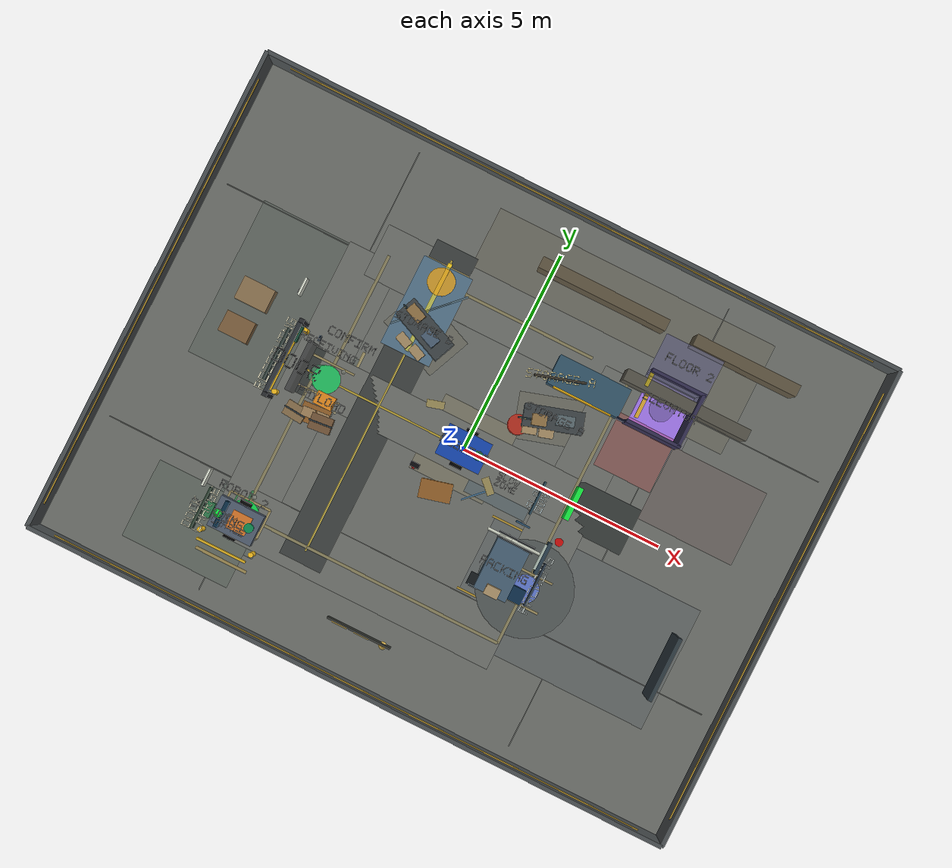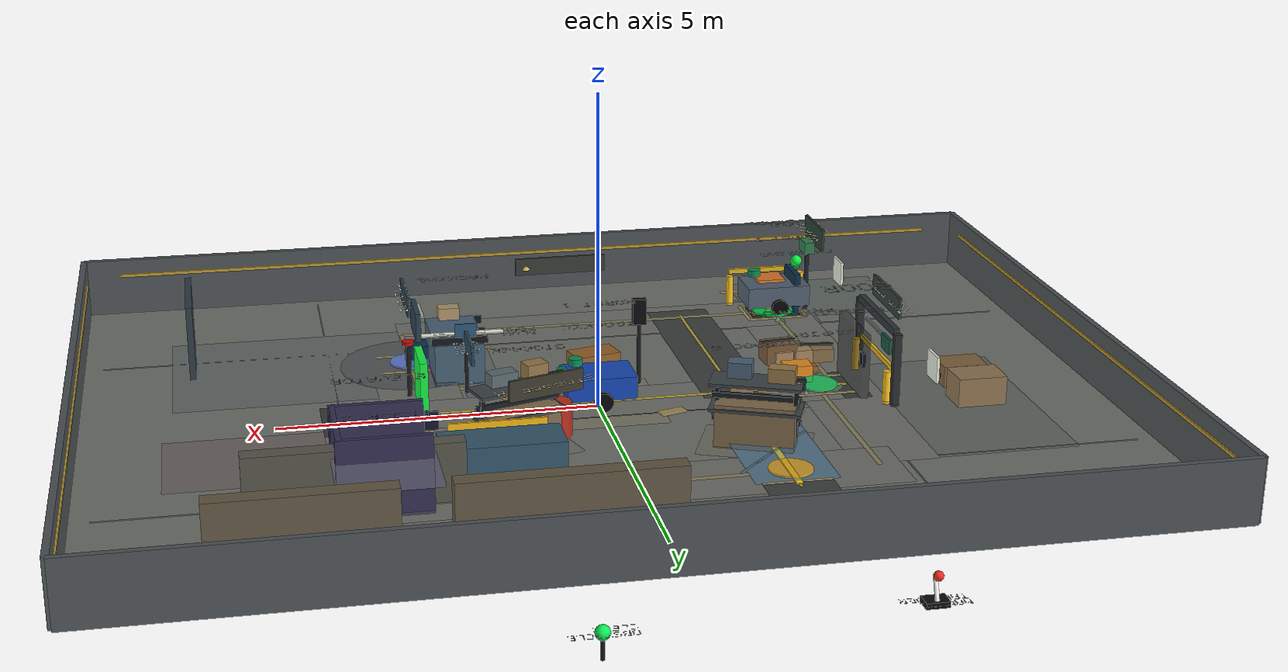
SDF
<sdf version="1.9">
 <world name="factory_patrol">
  <physics name="default_physics" type="ode">
   <max_step_size>0.001</max_step_size>
   <real_time_factor>1.0</real_time_factor>
  </physics>
  <plugin filename="gz-sim-physics-system" name="gz::sim::systems::Physics"/>
  <plugin filename="gz-sim-user-commands-system" name="gz::sim::systems::UserCommands"/>
  <plugin filename="gz-sim-scene-broadcaster-system" name="gz::sim::systems::SceneBroadcaster"/>
  <plugin filename="gz-sim-imu-system" name="gz::sim::systems::Imu"/>
  <plugin filename="gz-sim-sensors-system" name="gz::sim::systems::Sensors">
   <render_engine>ogre2</render_engine>
  </plugin>
  <scene>
   <ambient>0.54 0.55 0.55 1</ambient>
   <background>0.74 0.76 0.76 1</background>
   <shadows>true</shadows>
  </scene>
  <model name="factory_patrol_main_road">
   <static>true</static>
   <pose>0 0 0.062 0 0 0</pose>
   <link name="link">
    <visual name="east_west_main_patrol_road">
     <geometry><box><size>8.6 1.15 0.018</size></box></geometry>
     <material><ambient>0.18 0.20 0.20 0.72</ambient><diffuse>0.18 0.20 0.20 0.72</diffuse></material>
    </visual>
    <visual name="north_south_service_road">
     <pose>-2.2 0 0.004 0 0 0</pose>
     <geometry><box><size>1.05 8.1 0.018</size></box></geometry>
     <material><ambient>0.18 0.20 0.20 0.64</ambient><diffuse>0.18 0.20 0.20 0.64</diffuse></material>
    </visual>
    <visual name="turning_area">
     <pose>2.7 -2.25 0.008 0 0 0</pose>
     <geometry><cylinder><radius>1.15</radius><length>0.02</length></cylinder></geometry>
     <material><ambient>0.24 0.28 0.30 0.42</ambient><diffuse>0.24 0.28 0.30 0.42</diffuse></material>
    </visual>
   </link>
  </model>
  <model name="factory_patrol_lane_markers">
   <static>true</static>
   <pose>0 0 0.084 0 0 0</pose>
   <link name="link">
    <visual name="center_lane_main">
     <geometry><box><size>8.1 0.045 0.018</size></box></geometry>
     <material><diffuse>0.92 0.78 0.18 0.72</diffuse><emissive>0.16 0.10 0.00 1</emissive></material>
    </visual>
    <visual name="center_lane_service">
     <pose>-2.2 0 0.004 0 0 1.5708</pose>
     <geometry><box><size>7.5 0.045 0.018</size></box></geometry>
     <material><diffuse>0.92 0.78 0.18 0.62</diffuse><emissive>0.16 0.10 0.00 1</emissive></material>
    </visual>
    <visual name="narrow_corridor_marker">
     <pose>-2.2 2.55 0.01 0 0 1.5708</pose>
     <geometry><box><size>2.25 0.10 0.018</size></box></geometry>
     <material><diffuse>0.98 0.82 0.12 0.9</diffuse><emissive>0.2 0.1 0.0 1</emissive></material>
    </visual>
   </link>
  </model>
  <model name="factory_patrol_equipment_area">
   <static>true</static>
   <pose>1.9 2.55 0.34 0 0 0</pose>
   <link name="link">
    <collision name="equipment_bank_collision">
     <geometry><box><size>1.8 0.72 0.68</size></box></geometry>
    </collision>
    <visual name="equipment_bank_visual">
     <geometry><box><size>1.8 0.72 0.68</size></box></geometry>
     <material><diffuse>0.20 0.34 0.42 1</diffuse></material>
    </visual>
    <visual name="equipment_warning_panel">
     <pose>0 -0.38 0.32 0 0 0</pose>
     <geometry><box><size>1.45 0.035 0.24</size></box></geometry>
     <material><diffuse>0.95 0.72 0.08 1</diffuse><emissive>0.18 0.10 0.00 1</emissive></material>
    </visual>
   </link>
  </model>
  <model name="factory_patrol_static_obstacles">
   <static>true</static>
   <link name="link">
    <collision name="pallet_stack_a_collision">
     <pose>-0.15 -1.15 0.25 0 0 0.25</pose>
     <geometry><box><size>0.75 0.45 0.50</size></box></geometry>
    </collision>
    <visual name="pallet_stack_a">
     <pose>-0.15 -1.15 0.25 0 0 0.25</pose>
     <geometry><box><size>0.75 0.45 0.50</size></box></geometry>
     <material><diffuse>0.58 0.38 0.16 1</diffuse></material>
    </visual>
    <collision name="barrel_b_collision">
     <pose>0.85 1.05 0.28 0 0 0</pose>
     <geometry><cylinder><radius>0.24</radius><length>0.56</length></cylinder></geometry>
    </collision>
    <visual name="barrel_b">
     <pose>0.85 1.05 0.28 0 0 0</pose>
     <geometry><cylinder><radius>0.24</radius><length>0.56</length></cylinder></geometry>
     <material><diffuse>0.72 0.18 0.12 1</diffuse></material>
    </visual>
   </link>
  </model>
  <model name="geometry_validation_target">
   <static>true</static>
   <pose>2.76 0 0.66 0 0 0</pose>
   <link name="target_link">
    <visual name="target_visual">
     <geometry><box><size>0.12 0.80 0.80</size></box></geometry>
     <material>
      <ambient>0.08 0.80 0.20 1</ambient>
      <diffuse>0.08 0.95 0.25 1</diffuse>
      <emissive>0.02 0.18 0.04 1</emissive>
     </material>
    </visual>
   </link>
  </model>
  <model name="factory_patrol_zone_overlays">
   <static>true</static>
   <pose>0 0 0.096 0 0 0</pose>
   <link name="link">
    <visual name="slow_zone_visual">
     <pose>-2.2 2.45 0 0 0 0</pose>
     <geometry><box><size>1.25 2.25 0.018</size></box></geometry>
     <material><diffuse>0.08 0.56 1.00 0.24</diffuse><ambient>0.08 0.56 1.00 0.24</ambient></material>
    </visual>
    <visual name="no_go_zone_planned_visual">
     <pose>3.55 1.70 0.006 0 0 0</pose>
     <geometry><box><size>1.45 1.35 0.018</size></box></geometry>
     <material><diffuse>0.95 0.08 0.08 0.20</diffuse><ambient>0.95 0.08 0.08 0.20</ambient></material>
    </visual>
   </link>
  </model>
  <model name="factory_patrol_station_pads">
   <static>true</static>
   <pose>0 0 0.125 0 0 0</pose>
   <link name="link">
    <visual name="station_A_pad">
     <pose>-3.55 0.0 0 0 0 0</pose>
     <geometry><cylinder><radius>0.33</radius><length>0.035</length></cylinder></geometry>
     <material><diffuse>0.12 0.88 0.42 0.82</diffuse><emissive>0.00 0.22 0.08 1</emissive></material>
    </visual>
    <visual name="station_B_pad">
     <pose>-2.2 3.2 0 0 0 0</pose>
     <geometry><cylinder><radius>0.33</radius><length>0.035</length></cylinder></geometry>
     <material><diffuse>0.95 0.70 0.16 0.82</diffuse><emissive>0.22 0.10 0.00 1</emissive></material>
    </visual>
    <visual name="station_C_pad">
     <pose>2.7 -2.25 0 0 0 0</pose>
     <geometry><cylinder><radius>0.33</radius><length>0.035</length></cylinder></geometry>
     <material><diffuse>0.42 0.54 0.95 0.82</diffuse><emissive>0.04 0.08 0.24 1</emissive></material>
    </visual>
    <visual name="factory_dock_pad">
     <pose>-3.85 -3.65 0 0 0 0</pose>
     <geometry><cylinder><radius>0.36</radius><length>0.035</length></cylinder></geometry>
     <material><diffuse>0.06 0.95 0.34 0.88</diffuse><emissive>0.00 0.28 0.08 1</emissive></material>
    </visual>
   </link>
  </model>
  <light name="sun" type="directional">
   <pose>0 0 10 0 0 0</pose>
   <diffuse>0.95 0.95 0.92 1</diffuse>
   <specular>0.28 0.28 0.26 1</specular>
   <direction>-0.5 0.1 -1</direction>
  </light>
  <light name="soft_fill_light" type="point">
   <pose>0 -2 5 0 0 0</pose>
   <diffuse>0.45 0.48 0.52 1</diffuse>
   <specular>0.08 0.08 0.08 1</specular>
   <attenuation>
    <range>12</range>
    <constant>0.8</constant>
    <linear>0.03</linear>
    <quadratic>0.002</quadratic>
   </attenuation>
  </light>
  <model name="floor">
   <static>true</static>
   <link name="link">
    <collision name="collision"><geometry><box><size>16 12 0.05</size></box></geometry></collision>
    <visual name="visual">
     <geometry><box><size>16 12 0.05</size></box></geometry>
     <material>
      <ambient>0.43 0.44 0.42 1</ambient>
      <diffuse>0.43 0.44 0.42 1</diffuse>
      <specular>0.03 0.03 0.03 1</specular>
     </material>
    </visual>
   </link>
  </model>
  <model name="north_wall">
   <static>true</static>
   <pose>0 6 0.5 0 0 0</pose>
   <link name="link">
    <collision name="c"><geometry><box><size>16 0.1 1</size></box></geometry></collision>
    <visual name="v">
     <geometry><box><size>16 0.1 1</size></box></geometry>
     <material><diffuse>0.30 0.32 0.33 1</diffuse></material>
    </visual>
   </link>
  </model>
  <model name="south_wall">
   <static>true</static>
   <pose>0 -6 0.5 0 0 0</pose>
   <link name="link">
    <collision name="c"><geometry><box><size>16 0.1 1</size></box></geometry></collision>
    <visual name="v">
     <geometry><box><size>16 0.1 1</size></box></geometry>
     <material><diffuse>0.30 0.32 0.33 1</diffuse></material>
    </visual>
   </link>
  </model>
  <model name="east_wall">
   <static>true</static>
   <pose>8 0 0.5 0 0 0</pose>
   <link name="link">
    <collision name="c"><geometry><box><size>0.1 12 1</size></box></geometry></collision>
    <visual name="v">
     <geometry><box><size>0.1 12 1</size></box></geometry>
     <material><diffuse>0.30 0.32 0.33 1</diffuse></material>
    </visual>
   </link>
  </model>
  <model name="west_wall">
   <static>true</static>
   <pose>-8 0 0.5 0 0 0</pose>
   <link name="link">
    <collision name="c"><geometry><box><size>0.1 12 1</size></box></geometry></collision>
    <visual name="v">
     <geometry><box><size>0.1 12 1</size></box></geometry>
     <material><diffuse>0.30 0.32 0.33 1</diffuse></material>
    </visual>
   </link>
  </model>
  <model name="showcase_large_factory_layout">
   <static>true</static>
   <pose>0 0 0.052 0 0 0</pose>
   <link name="link">
    <visual name="receiving_area_large">
     <pose>-5.35 1.10 0 0 0 0</pose>
     <geometry><box><size>2.70 3.90 0.012</size></box></geometry>
     <material><diffuse>0.25 0.34 0.30 0.16</diffuse><ambient>0.25 0.34 0.30 0.16</ambient></material>
    </visual>
    <visual name="storage_area_large">
     <pose>1.80 3.95 0.002 0 0 0</pose>
     <geometry><box><size>7.10 2.80 0.012</size></box></geometry>
     <material><diffuse>0.45 0.40 0.30 0.15</diffuse><ambient>0.45 0.40 0.30 0.15</ambient></material>
    </visual>
    <visual name="packing_area_large">
     <pose>4.65 -2.40 0.004 0 0 0</pose>
     <geometry><box><size>3.80 3.05 0.012</size></box></geometry>
     <material><diffuse>0.27 0.33 0.39 0.16</diffuse><ambient>0.27 0.33 0.39 0.16</ambient></material>
    </visual>
    <visual name="dock_area_large">
     <pose>-4.80 -4.35 0.006 0 0 0</pose>
     <geometry><box><size>2.70 1.95 0.012</size></box></geometry>
     <material><diffuse>0.25 0.36 0.30 0.18</diffuse><ambient>0.25 0.36 0.30 0.18</ambient></material>
    </visual>
    <visual name="restricted_service_area_large">
     <pose>5.50 1.30 0.008 0 0 0</pose>
     <geometry><box><size>2.40 1.85 0.012</size></box></geometry>
     <material><diffuse>0.42 0.25 0.25 0.13</diffuse><ambient>0.42 0.25 0.25 0.13</ambient></material>
    </visual>
    <visual name="aisle_left_band">
     <pose>-3.85 -0.35 0.010 0 0 1.5708</pose>
     <geometry><box><size>6.90 1.30 0.010</size></box></geometry>
     <material><diffuse>0.50 0.51 0.48 0.13</diffuse><ambient>0.50 0.51 0.48 0.13</ambient></material>
    </visual>
    <visual name="aisle_back_band">
     <pose>-0.20 3.20 0.012 0 0 0</pose>
     <geometry><box><size>7.35 1.30 0.010</size></box></geometry>
     <material><diffuse>0.50 0.51 0.48 0.13</diffuse><ambient>0.50 0.51 0.48 0.13</ambient></material>
    </visual>
    <visual name="aisle_right_drop_band">
     <pose>2.70 0.45 0.014 0 0 1.5708</pose>
     <geometry><box><size>5.50 1.30 0.010</size></box></geometry>
     <material><diffuse>0.50 0.51 0.48 0.13</diffuse><ambient>0.50 0.51 0.48 0.13</ambient></material>
    </visual>
    <visual name="aisle_return_band">
     <pose>-0.55 -3.65 0.016 0 0 0</pose>
     <geometry><box><size>6.60 1.30 0.010</size></box></geometry>
     <material><diffuse>0.50 0.51 0.48 0.13</diffuse><ambient>0.50 0.51 0.48 0.13</ambient></material>
    </visual>
    <visual name="aisle_center_cross_band">
     <pose>-0.55 0.00 0.018 0 0 0</pose>
     <geometry><box><size>6.60 1.15 0.010</size></box></geometry>
     <material><diffuse>0.50 0.51 0.48 0.10</diffuse><ambient>0.50 0.51 0.48 0.10</ambient></material>
    </visual>
    <visual name="route_dock_to_receiving">
     <pose>-3.85 -1.82 0.026 0 0 1.5708</pose>
     <geometry><box><size>3.66 0.070 0.018</size></box></geometry>
     <material><diffuse>0.66 0.60 0.38 0.62</diffuse><emissive>0.06 0.04 0.00 1</emissive></material>
    </visual>
    <visual name="route_receiving_to_back">
     <pose>-3.55 1.60 0.028 0 0 1.5708</pose>
     <geometry><box><size>3.20 0.070 0.018</size></box></geometry>
     <material><diffuse>0.66 0.60 0.38 0.62</diffuse><emissive>0.06 0.04 0.00 1</emissive></material>
    </visual>
    <visual name="route_back_storage">
     <pose>-0.42 3.20 0.030 0 0 0</pose>
     <geometry><box><size>4.26 0.070 0.018</size></box></geometry>
     <material><diffuse>0.66 0.60 0.38 0.62</diffuse><emissive>0.06 0.04 0.00 1</emissive></material>
    </visual>
    <visual name="route_storage_to_packing">
     <pose>2.70 0.48 0.032 0 0 1.5708</pose>
     <geometry><box><size>5.44 0.070 0.018</size></box></geometry>
     <material><diffuse>0.66 0.60 0.38 0.62</diffuse><emissive>0.06 0.04 0.00 1</emissive></material>
    </visual>
    <visual name="route_packing_to_return">
     <pose>2.70 -2.95 0.034 0 0 1.5708</pose>
     <geometry><box><size>1.40 0.070 0.018</size></box></geometry>
     <material><diffuse>0.66 0.60 0.38 0.62</diffuse><emissive>0.06 0.04 0.00 1</emissive></material>
    </visual>
    <visual name="route_return_to_dock">
     <pose>-0.58 -3.65 0.036 0 0 0</pose>
     <geometry><box><size>6.55 0.070 0.018</size></box></geometry>
     <material><diffuse>0.66 0.60 0.38 0.62</diffuse><emissive>0.06 0.04 0.00 1</emissive></material>
    </visual>
    <visual name="station_frame_dock_n">
     <pose>-3.85 -3.28 0.040 0 0 0</pose>
     <geometry><box><size>1.02 0.050 0.018</size></box></geometry>
     <material><diffuse>0.73 0.65 0.40 0.76</diffuse></material>
    </visual>
    <visual name="station_frame_dock_s">
     <pose>-3.85 -4.02 0.040 0 0 0</pose>
     <geometry><box><size>1.02 0.050 0.018</size></box></geometry>
     <material><diffuse>0.73 0.65 0.40 0.76</diffuse></material>
    </visual>
    <visual name="station_frame_dock_e">
     <pose>-3.34 -3.65 0.040 0 0 1.5708</pose>
     <geometry><box><size>0.74 0.050 0.018</size></box></geometry>
     <material><diffuse>0.73 0.65 0.40 0.76</diffuse></material>
    </visual>
    <visual name="station_frame_dock_w">
     <pose>-4.36 -3.65 0.040 0 0 1.5708</pose>
     <geometry><box><size>0.74 0.050 0.018</size></box></geometry>
     <material><diffuse>0.73 0.65 0.40 0.76</diffuse></material>
    </visual>
    <visual name="station_frame_receiving_n">
     <pose>-3.55 0.38 0.040 0 0 0</pose>
     <geometry><box><size>1.05 0.050 0.018</size></box></geometry>
     <material><diffuse>0.73 0.65 0.40 0.72</diffuse></material>
    </visual>
    <visual name="station_frame_receiving_s">
     <pose>-3.55 -0.38 0.040 0 0 0</pose>
     <geometry><box><size>1.05 0.050 0.018</size></box></geometry>
     <material><diffuse>0.73 0.65 0.40 0.72</diffuse></material>
    </visual>
    <visual name="station_frame_storage_n">
     <pose>-2.20 3.58 0.040 0 0 0</pose>
     <geometry><box><size>1.05 0.050 0.018</size></box></geometry>
     <material><diffuse>0.73 0.65 0.40 0.72</diffuse></material>
    </visual>
    <visual name="station_frame_storage_s">
     <pose>-2.20 2.82 0.040 0 0 0</pose>
     <geometry><box><size>1.05 0.050 0.018</size></box></geometry>
     <material><diffuse>0.73 0.65 0.40 0.72</diffuse></material>
    </visual>
    <visual name="station_frame_packing_n">
     <pose>2.70 -1.87 0.040 0 0 0</pose>
     <geometry><box><size>1.05 0.050 0.018</size></box></geometry>
     <material><diffuse>0.73 0.65 0.40 0.72</diffuse></material>
    </visual>
    <visual name="station_frame_packing_s">
     <pose>2.70 -2.63 0.040 0 0 0</pose>
     <geometry><box><size>1.05 0.050 0.018</size></box></geometry>
     <material><diffuse>0.73 0.65 0.40 0.72</diffuse></material>
    </visual>
    <visual name="slow_zone_large_hatch_1">
     <pose>-2.45 2.20 0.048 0 0 0.7854</pose>
     <geometry><box><size>1.05 0.045 0.018</size></box></geometry>
     <material><diffuse>0.24 0.44 0.56 0.48</diffuse></material>
    </visual>
    <visual name="slow_zone_large_hatch_2">
     <pose>-2.15 2.50 0.048 0 0 0.7854</pose>
     <geometry><box><size>1.05 0.045 0.018</size></box></geometry>
     <material><diffuse>0.24 0.44 0.56 0.48</diffuse></material>
    </visual>
    <visual name="slow_zone_large_hatch_3">
     <pose>-1.85 2.80 0.048 0 0 0.7854</pose>
     <geometry><box><size>1.05 0.045 0.018</size></box></geometry>
     <material><diffuse>0.24 0.44 0.56 0.48</diffuse></material>
    </visual>
    <visual name="storage_showcase_rack_a">
     <pose>1.25 4.55 0.45 0 0 0</pose>
     <geometry><box><size>3.20 0.28 0.90</size></box></geometry>
     <material><diffuse>0.38 0.34 0.26 1</diffuse></material>
    </visual>
    <visual name="storage_showcase_rack_b">
     <pose>4.85 4.55 0.45 0 0 0</pose>
     <geometry><box><size>2.60 0.28 0.90</size></box></geometry>
     <material><diffuse>0.38 0.34 0.26 1</diffuse></material>
    </visual>
    <visual name="storage_showcase_rack_c">
     <pose>4.05 3.15 0.45 0 0 0</pose>
     <geometry><box><size>3.10 0.28 0.90</size></box></geometry>
     <material><diffuse>0.34 0.33 0.29 1</diffuse></material>
    </visual>
    <visual name="receiving_inbound_buffer_1">
     <pose>-5.90 0.15 0.18 0 0 0</pose>
     <geometry><box><size>0.72 0.52 0.34</size></box></geometry>
     <material><diffuse>0.50 0.38 0.24 1</diffuse></material>
    </visual>
    <visual name="receiving_inbound_buffer_2">
     <pose>-5.85 1.00 0.24 0 0 0</pose>
     <geometry><box><size>0.78 0.56 0.46</size></box></geometry>
     <material><diffuse>0.56 0.46 0.32 1</diffuse></material>
    </visual>
    <visual name="packing_showcase_toolwall">
     <pose>6.20 -2.38 0.85 0 0 0</pose>
     <geometry><box><size>0.10 1.55 1.20</size></box></geometry>
     <material><diffuse>0.18 0.23 0.26 1</diffuse></material>
    </visual>
    <visual name="dock_approach_stop_bar">
     <pose>-3.85 -4.80 0.052 0 0 0</pose>
     <geometry><box><size>1.30 0.070 0.018</size></box></geometry>
     <material><diffuse>0.72 0.62 0.34 0.78</diffuse></material>
    </visual>
   </link>
  </model>
  <model name="storage_rack_1">
   <static>true</static>
   <pose>1.5 1.5 0.35 0 0 0.3</pose>
   <link name="link">
    <collision name="c"><geometry><box><size>1.2 0.45 0.7</size></box></geometry></collision>
    <visual name="v">
     <geometry><box><size>1.2 0.45 0.7</size></box></geometry>
     <material><diffuse>0.50 0.42 0.30 1</diffuse></material>
    </visual>
   </link>
  </model>
  <model name="storage_rack_2">
   <static>true</static>
   <pose>-2 2 0.35 0 0 -0.4</pose>
   <link name="link">
    <collision name="c"><geometry><box><size>1.2 0.5 0.7</size></box></geometry></collision>
    <visual name="v">
     <geometry><box><size>1.2 0.5 0.7</size></box></geometry>
     <material><diffuse>0.50 0.42 0.30 1</diffuse></material>
    </visual>
   </link>
  </model>
  <model name="packing_table">
   <static>true</static>
   <pose>2 -2 0.35 0 0 0.0</pose>
   <link name="link">
    <collision name="c"><geometry><box><size>0.8 1.4 0.7</size></box></geometry></collision>
    <visual name="v">
     <geometry><box><size>0.8 1.4 0.7</size></box></geometry>
     <material><diffuse>0.28 0.38 0.46 1</diffuse></material>
    </visual>
   </link>
  </model>
  <model name="showcase_rack_and_workcell_detail">
   <static>true</static>
   <link name="link">
    <visual name="rack_a_top_beam">
     <pose>1.50 1.50 0.78 0 0 0.30</pose>
     <geometry><box><size>1.34 0.06 0.08</size></box></geometry>
     <material><diffuse>0.10 0.12 0.14 1</diffuse></material>
    </visual>
    <visual name="rack_a_bottom_beam">
     <pose>1.50 1.50 0.42 0 0 0.30</pose>
     <geometry><box><size>1.34 0.06 0.08</size></box></geometry>
     <material><diffuse>0.10 0.12 0.14 1</diffuse></material>
    </visual>
    <visual name="rack_a_post_1">
     <pose>0.94 1.31 0.55 0 0 0.30</pose>
     <geometry><box><size>0.07 0.07 0.72</size></box></geometry>
     <material><diffuse>0.08 0.09 0.10 1</diffuse></material>
    </visual>
    <visual name="rack_a_post_2">
     <pose>2.06 1.69 0.55 0 0 0.30</pose>
     <geometry><box><size>0.07 0.07 0.72</size></box></geometry>
     <material><diffuse>0.08 0.09 0.10 1</diffuse></material>
    </visual>
    <visual name="rack_b_top_beam">
     <pose>-2.00 2.00 0.78 0 0 -0.40</pose>
     <geometry><box><size>1.34 0.06 0.08</size></box></geometry>
     <material><diffuse>0.10 0.12 0.14 1</diffuse></material>
    </visual>
    <visual name="rack_b_bottom_beam">
     <pose>-2.00 2.00 0.42 0 0 -0.40</pose>
     <geometry><box><size>1.34 0.06 0.08</size></box></geometry>
     <material><diffuse>0.10 0.12 0.14 1</diffuse></material>
    </visual>
    <visual name="rack_b_post_1">
     <pose>-2.54 2.24 0.55 0 0 -0.40</pose>
     <geometry><box><size>0.07 0.07 0.72</size></box></geometry>
     <material><diffuse>0.08 0.09 0.10 1</diffuse></material>
    </visual>
    <visual name="rack_b_post_2">
     <pose>-1.46 1.76 0.55 0 0 -0.40</pose>
     <geometry><box><size>0.07 0.07 0.72</size></box></geometry>
     <material><diffuse>0.08 0.09 0.10 1</diffuse></material>
    </visual>
    <visual name="packing_conveyor">
     <pose>2.00 -1.36 0.78 0 0 0</pose>
     <geometry><box><size>0.90 0.16 0.12</size></box></geometry>
     <material><diffuse>0.07 0.08 0.09 1</diffuse></material>
    </visual>
    <visual name="packing_roller_1">
     <pose>1.70 -1.36 0.87 0 1.5708 0</pose>
     <geometry><cylinder><radius>0.035</radius><length>0.82</length></cylinder></geometry>
     <material><diffuse>0.80 0.82 0.76 1</diffuse></material>
    </visual>
    <visual name="packing_roller_2">
     <pose>2.00 -1.36 0.87 0 1.5708 0</pose>
     <geometry><cylinder><radius>0.035</radius><length>0.82</length></cylinder></geometry>
     <material><diffuse>0.80 0.82 0.76 1</diffuse></material>
    </visual>
    <visual name="packing_roller_3">
     <pose>2.30 -1.36 0.87 0 1.5708 0</pose>
     <geometry><cylinder><radius>0.035</radius><length>0.82</length></cylinder></geometry>
     <material><diffuse>0.80 0.82 0.76 1</diffuse></material>
    </visual>
   </link>
  </model>
  <model name="showcase_zone_floor">
   <static>true</static>
   <pose>0 0 0.035 0 0 0</pose>
   <link name="link">
    <visual name="receiving_zone">
     <pose>-3.70 0.00 0 0 0 0</pose>
     <geometry><box><size>1.25 1.50 0.012</size></box></geometry>
     <material><diffuse>0.28 0.36 0.32 0.20</diffuse><ambient>0.28 0.36 0.32 0.20</ambient></material>
    </visual>
    <visual name="storage_a_zone">
     <pose>1.50 1.50 0 0 0 0.30</pose>
     <geometry><box><size>1.65 1.10 0.012</size></box></geometry>
     <material><diffuse>0.48 0.43 0.32 0.20</diffuse><ambient>0.48 0.43 0.32 0.20</ambient></material>
    </visual>
    <visual name="storage_b_zone">
     <pose>-2.00 2.00 0 0 0 -0.40</pose>
     <geometry><box><size>1.65 1.15 0.012</size></box></geometry>
     <material><diffuse>0.48 0.43 0.32 0.20</diffuse><ambient>0.48 0.43 0.32 0.20</ambient></material>
    </visual>
    <visual name="packing_zone">
     <pose>2.00 -2.00 0 0 0 0</pose>
     <geometry><box><size>1.30 1.85 0.012</size></box></geometry>
     <material><diffuse>0.30 0.36 0.42 0.20</diffuse><ambient>0.30 0.36 0.42 0.20</ambient></material>
    </visual>
    <visual name="dock_zone">
     <pose>-3.90 -3.80 0 0 0 0</pose>
     <geometry><box><size>1.35 1.35 0.012</size></box></geometry>
     <material><diffuse>0.28 0.38 0.32 0.22</diffuse><ambient>0.28 0.38 0.32 0.22</ambient></material>
    </visual>
    <visual name="elevator_zone">
     <pose>3.65 2.85 0 0 0 0</pose>
     <geometry><box><size>1.70 2.30 0.012</size></box></geometry>
     <material><diffuse>0.46 0.42 0.62 0.15</diffuse><ambient>0.46 0.42 0.62 0.15</ambient></material>
    </visual>
    <visual name="traffic_control_zone">
     <pose>0.00 0.00 0.006 0 0 0</pose>
     <geometry><box><size>1.90 1.90 0.012</size></box></geometry>
     <material><diffuse>0.72 0.64 0.40 0.14</diffuse><ambient>0.72 0.64 0.40 0.14</ambient></material>
    </visual>
    <visual name="slow_zone_overlay">
     <pose>1.20 -0.25 0.012 0 0 0</pose>
     <geometry><box><size>1.55 1.25 0.012</size></box></geometry>
     <material><diffuse>0.22 0.38 0.48 0.24</diffuse><ambient>0.22 0.38 0.48 0.24</ambient></material>
    </visual>
   </link>
  </model>
  <model name="showcase_floor_finish">
   <static>true</static>
   <pose>0 0 0.057 0 0 0</pose>
   <link name="link">
    <visual name="floor_joint_x_neg">
     <pose>-4.00 0 0 0 0 0</pose>
     <geometry><box><size>0.018 11.30 0.010</size></box></geometry>
     <material><diffuse>0.28 0.29 0.28 0.42</diffuse><ambient>0.28 0.29 0.28 0.42</ambient></material>
    </visual>
    <visual name="floor_joint_x_pos">
     <pose>4.00 0 0 0 0 0</pose>
     <geometry><box><size>0.018 11.30 0.010</size></box></geometry>
     <material><diffuse>0.28 0.29 0.28 0.42</diffuse><ambient>0.28 0.29 0.28 0.42</ambient></material>
    </visual>
    <visual name="floor_joint_y_neg">
     <pose>0 -3.00 0 0 0 0</pose>
     <geometry><box><size>15.30 0.018 0.010</size></box></geometry>
     <material><diffuse>0.28 0.29 0.28 0.42</diffuse><ambient>0.28 0.29 0.28 0.42</ambient></material>
    </visual>
    <visual name="floor_joint_y_pos">
     <pose>0 3.00 0 0 0 0</pose>
     <geometry><box><size>15.30 0.018 0.010</size></box></geometry>
     <material><diffuse>0.28 0.29 0.28 0.42</diffuse><ambient>0.28 0.29 0.28 0.42</ambient></material>
    </visual>
    <visual name="floor_tire_scuff_main_1">
     <pose>-0.55 -0.18 0.004 0 0 -0.01</pose>
     <geometry><box><size>6.80 0.035 0.010</size></box></geometry>
     <material><diffuse>0.22 0.23 0.22 0.26</diffuse><ambient>0.22 0.23 0.22 0.26</ambient></material>
    </visual>
    <visual name="floor_tire_scuff_main_2">
     <pose>-0.42 0.20 0.004 0 0 -0.01</pose>
     <geometry><box><size>6.40 0.028 0.010</size></box></geometry>
     <material><diffuse>0.22 0.23 0.22 0.22</diffuse><ambient>0.22 0.23 0.22 0.22</ambient></material>
    </visual>
    <visual name="floor_tire_scuff_dock_1">
     <pose>-3.88 -2.10 0.004 0 0 1.5708</pose>
     <geometry><box><size>3.20 0.030 0.010</size></box></geometry>
     <material><diffuse>0.22 0.23 0.22 0.24</diffuse><ambient>0.22 0.23 0.22 0.24</ambient></material>
    </visual>
    <visual name="floor_tire_scuff_packing_1">
     <pose>2.70 -1.60 0.004 0 0 -1.5708</pose>
     <geometry><box><size>3.20 0.025 0.010</size></box></geometry>
     <material><diffuse>0.22 0.23 0.22 0.22</diffuse><ambient>0.22 0.23 0.22 0.22</ambient></material>
    </visual>
   </link>
  </model>
  <model name="showcase_lane_markers">
   <static>true</static>
   <pose>0 0 0.055 0 0 0</pose>
   <link name="link">
    <visual name="lane_dock_receiving">
     <pose>-3.90 -1.84 0 0 0 1.5708</pose>
     <geometry><box><size>3.62 0.045 0.018</size></box></geometry>
     <material><diffuse>0.60 0.62 0.58 0.20</diffuse><emissive>0.03 0.03 0.03 1</emissive></material>
    </visual>
    <visual name="lane_receiving_storage_a">
     <pose>-3.55 1.60 0 0 0 1.5708</pose>
     <geometry><box><size>3.20 0.045 0.018</size></box></geometry>
     <material><diffuse>0.60 0.62 0.58 0.18</diffuse><emissive>0.03 0.03 0.03 1</emissive></material>
    </visual>
    <visual name="lane_receiving_storage_b">
     <pose>-2.85 3.20 0 0 0 0</pose>
     <geometry><box><size>1.40 0.045 0.018</size></box></geometry>
     <material><diffuse>0.60 0.62 0.58 0.18</diffuse><emissive>0.03 0.03 0.03 1</emissive></material>
    </visual>
    <visual name="lane_storage_a_packing">
     <pose>0.25 3.20 0 0 0 0</pose>
     <geometry><box><size>4.90 0.045 0.018</size></box></geometry>
     <material><diffuse>0.60 0.62 0.58 0.18</diffuse><emissive>0.03 0.03 0.03 1</emissive></material>
    </visual>
    <visual name="lane_storage_b_packing">
     <pose>2.70 0.48 0.004 0 0 1.5708</pose>
     <geometry><box><size>5.44 0.045 0.018</size></box></geometry>
     <material><diffuse>0.60 0.62 0.58 0.18</diffuse><emissive>0.03 0.03 0.03 1</emissive></material>
    </visual>
    <visual name="lane_packing_dock">
     <pose>-0.58 -3.65 0 0 0 0</pose>
     <geometry><box><size>6.55 0.045 0.018</size></box></geometry>
     <material><diffuse>0.60 0.62 0.58 0.18</diffuse><emissive>0.03 0.03 0.03 1</emissive></material>
    </visual>
    <visual name="lane_packing_lift">
     <pose>2.70 -2.95 0 0 0 1.5708</pose>
     <geometry><box><size>1.40 0.045 0.018</size></box></geometry>
     <material><diffuse>0.60 0.62 0.58 0.18</diffuse><emissive>0.03 0.03 0.03 1</emissive></material>
    </visual>
    <visual name="lane_lift_floor2">
     <pose>3.65 3.35 0 0 0 1.5708</pose>
     <geometry><box><size>1.05 0.045 0.018</size></box></geometry>
     <material><diffuse>0.60 0.62 0.58 0.16</diffuse><emissive>0.02 0.02 0.02 1</emissive></material>
    </visual>
    <visual name="arrow_receiving">
     <pose>-3.28 0.34 0.020 0 0 0.78</pose>
     <geometry><cone><radius>0.11</radius><length>0.18</length></cone></geometry>
     <material><diffuse>0.64 0.66 0.60 0.55</diffuse><emissive>0.08 0.08 0.06 1</emissive></material>
    </visual>
    <visual name="arrow_packing">
     <pose>1.82 -1.36 0.020 0 0 -1.2</pose>
     <geometry><cone><radius>0.11</radius><length>0.18</length></cone></geometry>
     <material><diffuse>0.64 0.66 0.60 0.55</diffuse><emissive>0.08 0.08 0.06 1</emissive></material>
    </visual>
    <visual name="arrow_dock">
     <pose>-3.82 -3.18 0.020 0 0 -1.57</pose>
     <geometry><cone><radius>0.11</radius><length>0.18</length></cone></geometry>
     <material><diffuse>0.64 0.66 0.60 0.55</diffuse><emissive>0.08 0.08 0.06 1</emissive></material>
    </visual>
   </link>
  </model>
  <model name="showcase_station_pads">
   <static>true</static>
   <pose>0 0 0.070 0 0 0</pose>
   <link name="link">
    <visual name="pad_receiving">
     <pose>-3.70 0.00 0 0 0 0</pose>
     <geometry><cylinder><radius>0.28</radius><length>0.026</length></cylinder></geometry>
     <material><diffuse>0.20 0.52 0.34 0.58</diffuse><emissive>0.00 0.07 0.03 1</emissive></material>
    </visual>
    <visual name="pad_storage_a">
     <pose>1.50 1.50 0 0 0 0</pose>
     <geometry><cylinder><radius>0.28</radius><length>0.026</length></cylinder></geometry>
     <material><diffuse>0.54 0.46 0.28 0.50</diffuse><emissive>0.06 0.03 0.00 1</emissive></material>
    </visual>
    <visual name="pad_storage_b">
     <pose>-2.00 2.00 0 0 0 0</pose>
     <geometry><cylinder><radius>0.28</radius><length>0.026</length></cylinder></geometry>
     <material><diffuse>0.54 0.46 0.28 0.50</diffuse><emissive>0.06 0.03 0.00 1</emissive></material>
    </visual>
    <visual name="pad_packing">
     <pose>2.00 -2.00 0 0 0 0</pose>
     <geometry><cylinder><radius>0.28</radius><length>0.026</length></cylinder></geometry>
     <material><diffuse>0.26 0.40 0.52 0.50</diffuse><emissive>0.00 0.04 0.08 1</emissive></material>
    </visual>
    <visual name="pad_dock">
     <pose>-3.90 -3.80 0 0 0 0</pose>
     <geometry><cylinder><radius>0.28</radius><length>0.026</length></cylinder></geometry>
     <material><diffuse>0.18 0.58 0.30 0.58</diffuse><emissive>0.00 0.08 0.02 1</emissive></material>
    </visual>
    <visual name="pad_lift">
     <pose>3.65 2.85 0 0 0 0</pose>
     <geometry><cylinder><radius>0.28</radius><length>0.026</length></cylinder></geometry>
     <material><diffuse>0.42 0.36 0.60 0.55</diffuse><emissive>0.03 0.02 0.08 1</emissive></material>
    </visual>
    <visual name="wait_point_1">
     <pose>-1.05 0.62 0.012 0 0 0.28</pose>
     <geometry><box><size>0.42 0.18 0.026</size></box></geometry>
     <material><diffuse>0.78 0.68 0.34 0.60</diffuse><emissive>0.28 0.20 0.00 1</emissive></material>
    </visual>
    <visual name="wait_point_2">
     <pose>0.88 -0.52 0.012 0 0 -0.78</pose>
     <geometry><box><size>0.42 0.18 0.026</size></box></geometry>
     <material><diffuse>0.78 0.68 0.34 0.60</diffuse><emissive>0.28 0.20 0.00 1</emissive></material>
    </visual>
   </link>
  </model>
  <model name="showcase_pallets_and_totes">
   <static>true</static>
   <link name="link">
    <visual name="receiving_pallet">
     <pose>-3.42 -0.86 0.08 0 0 0.08</pose>
     <geometry><box><size>0.68 0.46 0.16</size></box></geometry>
     <material><diffuse>0.58 0.38 0.16 1</diffuse></material>
    </visual>
    <visual name="receiving_tote_1">
     <pose>-3.56 -0.86 0.30 0 0 0.08</pose>
     <geometry><box><size>0.30 0.22 0.22</size></box></geometry>
     <material><diffuse>0.64 0.52 0.36 1</diffuse></material>
    </visual>
    <visual name="receiving_tote_2">
     <pose>-3.22 -0.83 0.30 0 0 0.08</pose>
     <geometry><box><size>0.30 0.22 0.22</size></box></geometry>
     <material><diffuse>0.64 0.52 0.36 1</diffuse></material>
    </visual>
    <visual name="storage_a_tote_1">
     <pose>1.12 1.06 0.78 0 0 0.30</pose>
     <geometry><box><size>0.34 0.22 0.18</size></box></geometry>
     <material><diffuse>0.66 0.56 0.40 1</diffuse></material>
    </visual>
    <visual name="storage_a_tote_2">
     <pose>1.50 1.15 0.78 0 0 0.30</pose>
     <geometry><box><size>0.34 0.22 0.18</size></box></geometry>
     <material><diffuse>0.66 0.56 0.40 1</diffuse></material>
    </visual>
    <visual name="storage_b_tote_1">
     <pose>-2.32 1.58 0.78 0 0 -0.40</pose>
     <geometry><box><size>0.34 0.22 0.18</size></box></geometry>
     <material><diffuse>0.66 0.56 0.40 1</diffuse></material>
    </visual>
    <visual name="storage_b_tote_2">
     <pose>-1.94 1.46 0.78 0 0 -0.40</pose>
     <geometry><box><size>0.34 0.22 0.18</size></box></geometry>
     <material><diffuse>0.66 0.56 0.40 1</diffuse></material>
    </visual>
    <visual name="packing_bin">
     <pose>2.52 -2.45 0.18 0 0 0</pose>
     <geometry><box><size>0.46 0.36 0.36</size></box></geometry>
     <material><diffuse>0.05 0.18 0.30 1</diffuse></material>
    </visual>
    <visual name="packing_ready_tote">
     <pose>2.02 -2.60 0.82 0 0 0</pose>
     <geometry><box><size>0.34 0.24 0.20</size></box></geometry>
     <material><diffuse>0.68 0.58 0.42 1</diffuse></material>
    </visual>
   </link>
  </model>
  <model name="showcase_dock_guidance">
   <static>true</static>
   <pose>-3.90 -3.48 0.075 0 0 0</pose>
   <link name="link">
    <visual name="approach_lane">
     <pose>0 0 0 0 0 1.5708</pose>
     <geometry><box><size>0.86 0.06 0.024</size></box></geometry>
     <material><diffuse>0.22 0.58 0.32 0.74</diffuse><emissive>0.00 0.08 0.02 1</emissive></material>
    </visual>
    <visual name="left_alignment">
     <pose>-0.28 -0.10 0.006 0 0 1.5708</pose>
     <geometry><box><size>0.58 0.04 0.024</size></box></geometry>
     <material><diffuse>0.22 0.58 0.32 0.74</diffuse><emissive>0.00 0.08 0.02 1</emissive></material>
    </visual>
    <visual name="right_alignment">
     <pose>0.28 -0.10 0.006 0 0 1.5708</pose>
     <geometry><box><size>0.58 0.04 0.024</size></box></geometry>
     <material><diffuse>0.22 0.58 0.32 0.74</diffuse><emissive>0.00 0.08 0.02 1</emissive></material>
    </visual>
   </link>
  </model>
  <model name="showcase_environment_polish">
   <static>true</static>
   <link name="link">
    <visual name="north_wall_safety_stripe">
     <pose>0 5.935 0.72 0 0 0</pose>
     <geometry><box><size>14.80 0.026 0.055</size></box></geometry>
     <material><diffuse>0.72 0.58 0.18 1</diffuse><emissive>0.06 0.04 0.00 1</emissive></material>
    </visual>
    <visual name="south_wall_safety_stripe">
     <pose>0 -5.935 0.72 0 0 0</pose>
     <geometry><box><size>14.80 0.026 0.055</size></box></geometry>
     <material><diffuse>0.72 0.58 0.18 1</diffuse><emissive>0.06 0.04 0.00 1</emissive></material>
    </visual>
    <visual name="east_wall_safety_stripe">
     <pose>7.935 0 0.72 0 0 0</pose>
     <geometry><box><size>0.026 10.80 0.055</size></box></geometry>
     <material><diffuse>0.72 0.58 0.18 1</diffuse><emissive>0.06 0.04 0.00 1</emissive></material>
    </visual>
    <visual name="west_wall_safety_stripe">
     <pose>-7.935 0 0.72 0 0 0</pose>
     <geometry><box><size>0.026 10.80 0.055</size></box></geometry>
     <material><diffuse>0.72 0.58 0.18 1</diffuse><emissive>0.06 0.04 0.00 1</emissive></material>
    </visual>
    <visual name="dock_charge_mast">
     <pose>-4.48 -3.78 0.62 0 0 0</pose>
     <geometry><cylinder><radius>0.045</radius><length>1.12</length></cylinder></geometry>
     <material><diffuse>0.10 0.12 0.14 1</diffuse></material>
    </visual>
    <visual name="dock_charge_panel">
     <pose>-4.48 -3.78 1.22 0 0 0</pose>
     <geometry><box><size>0.18 0.36 0.20</size></box></geometry>
     <material><diffuse>0.18 0.48 0.30 0.95</diffuse><emissive>0.00 0.08 0.02 1</emissive></material>
    </visual>
    <visual name="door_keypad">
     <pose>-4.04 0.76 0.78 0 0 0</pose>
     <geometry><box><size>0.05 0.14 0.22</size></box></geometry>
     <material><diffuse>0.02 0.06 0.10 1</diffuse><emissive>0.00 0.18 0.28 1</emissive></material>
    </visual>
    <visual name="elevator_call_panel">
     <pose>2.86 2.18 0.86 0 0 0</pose>
     <geometry><box><size>0.20 0.05 0.28</size></box></geometry>
     <material><diffuse>0.06 0.08 0.16 1</diffuse><emissive>0.18 0.12 0.42 1</emissive></material>
    </visual>
    <visual name="traffic_light_pole">
     <pose>-0.82 -0.82 0.62 0 0 0</pose>
     <geometry><cylinder><radius>0.035</radius><length>1.18</length></cylinder></geometry>
     <material><diffuse>0.08 0.09 0.10 1</diffuse></material>
    </visual>
    <visual name="traffic_light_housing">
     <pose>-0.82 -0.82 1.25 0 0 0</pose>
     <geometry><box><size>0.22 0.12 0.42</size></box></geometry>
     <material><diffuse>0.04 0.04 0.05 1</diffuse></material>
    </visual>
    <visual name="traffic_light_red">
     <pose>-0.82 -0.88 1.36 0 0 0</pose>
     <geometry><sphere><radius>0.042</radius></sphere></geometry>
     <material><diffuse>0.70 0.08 0.06 1</diffuse><emissive>0.12 0.00 0.00 1</emissive></material>
    </visual>
    <visual name="traffic_light_yellow">
     <pose>-0.82 -0.88 1.25 0 0 0</pose>
     <geometry><sphere><radius>0.042</radius></sphere></geometry>
     <material><diffuse>0.78 0.58 0.12 1</diffuse><emissive>0.10 0.06 0.00 1</emissive></material>
    </visual>
    <visual name="traffic_light_green">
     <pose>-0.82 -0.88 1.14 0 0 0</pose>
     <geometry><sphere><radius>0.042</radius></sphere></geometry>
     <material><diffuse>0.16 0.58 0.28 1</diffuse><emissive>0.00 0.08 0.02 1</emissive></material>
    </visual>
    <visual name="speed_sign_pole">
     <pose>1.95 -0.92 0.55 0 0 0</pose>
     <geometry><cylinder><radius>0.032</radius><length>1.02</length></cylinder></geometry>
     <material><diffuse>0.08 0.09 0.10 1</diffuse></material>
    </visual>
    <visual name="speed_sign_panel">
     <pose>1.95 -0.92 1.08 0 0 0</pose>
     <geometry><box><size>0.34 0.035 0.22</size></box></geometry>
     <material><diffuse>0.18 0.34 0.46 0.96</diffuse><emissive>0.00 0.04 0.06 1</emissive></material>
    </visual>
    <visual name="receiving_bollard_1">
     <pose>-4.45 -0.78 0.28 0 0 0</pose>
     <geometry><cylinder><radius>0.06</radius><length>0.56</length></cylinder></geometry>
     <material><diffuse>0.98 0.76 0.12 1</diffuse><emissive>0.18 0.10 0.00 1</emissive></material>
    </visual>
    <visual name="receiving_bollard_2">
     <pose>-4.45 0.78 0.28 0 0 0</pose>
     <geometry><cylinder><radius>0.06</radius><length>0.56</length></cylinder></geometry>
     <material><diffuse>0.98 0.76 0.12 1</diffuse><emissive>0.18 0.10 0.00 1</emissive></material>
    </visual>
    <visual name="dock_bollard_1">
     <pose>-4.55 -4.35 0.28 0 0 0</pose>
     <geometry><cylinder><radius>0.06</radius><length>0.56</length></cylinder></geometry>
     <material><diffuse>0.98 0.76 0.12 1</diffuse><emissive>0.18 0.10 0.00 1</emissive></material>
    </visual>
    <visual name="dock_bollard_2">
     <pose>-3.25 -4.35 0.28 0 0 0</pose>
     <geometry><cylinder><radius>0.06</radius><length>0.56</length></cylinder></geometry>
     <material><diffuse>0.98 0.76 0.12 1</diffuse><emissive>0.18 0.10 0.00 1</emissive></material>
    </visual>
   </link>
  </model>
  <model name="showcase_receiving_inbound_detail">
   <static>true</static>
   <link name="link">
    <visual name="receiving_rollup_header">
     <pose>-4.54 0.00 1.22 0 0 0</pose>
     <geometry><box><size>0.10 1.72 0.12</size></box></geometry>
     <material><diffuse>0.18 0.20 0.22 1</diffuse></material>
    </visual>
    <visual name="receiving_rollup_left_post">
     <pose>-4.54 -0.92 0.62 0 0 0</pose>
     <geometry><box><size>0.12 0.10 1.18</size></box></geometry>
     <material><diffuse>0.16 0.17 0.18 1</diffuse></material>
    </visual>
    <visual name="receiving_rollup_right_post">
     <pose>-4.54 0.92 0.62 0 0 0</pose>
     <geometry><box><size>0.12 0.10 1.18</size></box></geometry>
     <material><diffuse>0.16 0.17 0.18 1</diffuse></material>
    </visual>
    <visual name="receiving_door_slat_1">
     <pose>-4.60 -0.46 0.90 0 0 0</pose>
     <geometry><box><size>0.035 0.62 0.045</size></box></geometry>
     <material><diffuse>0.48 0.50 0.50 1</diffuse></material>
    </visual>
    <visual name="receiving_door_slat_2">
     <pose>-4.60 0.18 0.90 0 0 0</pose>
     <geometry><box><size>0.035 0.62 0.045</size></box></geometry>
     <material><diffuse>0.48 0.50 0.50 1</diffuse></material>
    </visual>
    <visual name="receiving_buffer_floor_lane">
     <pose>-3.62 -0.58 0.030 0 0 0</pose>
     <geometry><box><size>1.22 0.09 0.018</size></box></geometry>
     <material><diffuse>0.78 0.72 0.52 0.58</diffuse><emissive>0.08 0.06 0.00 1</emissive></material>
    </visual>
    <visual name="receiving_buffer_floor_stop">
     <pose>-3.05 0.52 0.031 0 0 1.5708</pose>
     <geometry><box><size>0.86 0.07 0.018</size></box></geometry>
     <material><diffuse>0.80 0.72 0.44 0.62</diffuse><emissive>0.08 0.06 0.00 1</emissive></material>
    </visual>
    <visual name="receiving_floor_id_panel">
     <pose>-4.47 0.62 0.96 0 0 0</pose>
     <geometry><box><size>0.045 0.38 0.24</size></box></geometry>
     <material><diffuse>0.10 0.32 0.24 0.96</diffuse><emissive>0.00 0.08 0.04 1</emissive></material>
    </visual>
    <visual name="receiving_floor_id_bar_1">
     <pose>-4.49 0.52 0.99 0 0 0</pose>
     <geometry><box><size>0.052 0.14 0.035</size></box></geometry>
     <material><diffuse>0.88 0.92 0.82 1</diffuse></material>
    </visual>
    <visual name="receiving_floor_id_bar_2">
     <pose>-4.49 0.71 0.92 0 0 0</pose>
     <geometry><box><size>0.052 0.16 0.035</size></box></geometry>
     <material><diffuse>0.88 0.92 0.82 1</diffuse></material>
    </visual>
    <visual name="inbound_pallet_stack_1">
     <pose>-3.18 -0.96 0.36 0 0 0.10</pose>
     <geometry><box><size>0.52 0.38 0.32</size></box></geometry>
     <material><diffuse>0.46 0.34 0.22 1</diffuse></material>
    </visual>
    <visual name="inbound_pallet_stack_2">
     <pose>-3.84 -0.98 0.28 0 0 -0.08</pose>
     <geometry><box><size>0.50 0.36 0.22</size></box></geometry>
     <material><diffuse>0.54 0.44 0.30 1</diffuse></material>
    </visual>
    <visual name="inbound_wrap_band_1">
     <pose>-3.18 -0.96 0.54 0 0 0.10</pose>
     <geometry><box><size>0.56 0.035 0.035</size></box></geometry>
     <material><diffuse>0.18 0.22 0.24 1</diffuse></material>
    </visual>
    <visual name="inbound_wrap_band_2">
     <pose>-3.84 -0.98 0.42 0 0 -0.08</pose>
     <geometry><box><size>0.54 0.035 0.035</size></box></geometry>
     <material><diffuse>0.18 0.22 0.24 1</diffuse></material>
    </visual>
   </link>
  </model>
  <model name="showcase_storage_industrial_detail">
   <static>true</static>
   <link name="link">
    <visual name="rack_a_upper_shelf">
     <pose>1.50 1.50 1.02 0 0 0.30</pose>
     <geometry><box><size>1.38 0.52 0.045</size></box></geometry>
     <material><diffuse>0.24 0.27 0.28 1</diffuse></material>
    </visual>
    <visual name="rack_a_mid_shelf">
     <pose>1.50 1.50 0.62 0 0 0.30</pose>
     <geometry><box><size>1.38 0.52 0.045</size></box></geometry>
     <material><diffuse>0.24 0.27 0.28 1</diffuse></material>
    </visual>
    <visual name="rack_a_load_1">
     <pose>1.22 1.33 1.20 0 0 0.30</pose>
     <geometry><box><size>0.34 0.26 0.24</size></box></geometry>
     <material><diffuse>0.58 0.46 0.28 1</diffuse></material>
    </visual>
    <visual name="rack_a_load_2">
     <pose>1.75 1.57 1.20 0 0 0.30</pose>
     <geometry><box><size>0.42 0.24 0.20</size></box></geometry>
     <material><diffuse>0.36 0.42 0.44 1</diffuse></material>
    </visual>
    <visual name="rack_a_id_plate">
     <pose>0.91 1.23 1.02 0 0 0.30</pose>
     <geometry><box><size>0.32 0.035 0.18</size></box></geometry>
     <material><diffuse>0.12 0.18 0.20 1</diffuse><emissive>0.02 0.04 0.04 1</emissive></material>
    </visual>
    <visual name="rack_a_id_mark">
     <pose>0.91 1.23 1.04 0 0 0.30</pose>
     <geometry><box><size>0.22 0.042 0.032</size></box></geometry>
     <material><diffuse>0.86 0.78 0.42 1</diffuse></material>
    </visual>
    <visual name="rack_b_upper_shelf">
     <pose>-2.00 2.00 1.02 0 0 -0.40</pose>
     <geometry><box><size>1.38 0.56 0.045</size></box></geometry>
     <material><diffuse>0.24 0.27 0.28 1</diffuse></material>
    </visual>
    <visual name="rack_b_mid_shelf">
     <pose>-2.00 2.00 0.62 0 0 -0.40</pose>
     <geometry><box><size>1.38 0.56 0.045</size></box></geometry>
     <material><diffuse>0.24 0.27 0.28 1</diffuse></material>
    </visual>
    <visual name="rack_b_load_1">
     <pose>-2.32 2.22 1.20 0 0 -0.40</pose>
     <geometry><box><size>0.40 0.24 0.22</size></box></geometry>
     <material><diffuse>0.58 0.46 0.28 1</diffuse></material>
    </visual>
    <visual name="rack_b_load_2">
     <pose>-1.78 1.86 1.20 0 0 -0.40</pose>
     <geometry><box><size>0.36 0.26 0.24</size></box></geometry>
     <material><diffuse>0.30 0.38 0.46 1</diffuse></material>
    </visual>
    <visual name="rack_b_id_plate">
     <pose>-2.52 2.22 1.02 0 0 -0.40</pose>
     <geometry><box><size>0.32 0.035 0.18</size></box></geometry>
     <material><diffuse>0.12 0.18 0.20 1</diffuse><emissive>0.02 0.04 0.04 1</emissive></material>
    </visual>
    <visual name="rack_b_id_mark">
     <pose>-2.52 2.22 1.04 0 0 -0.40</pose>
     <geometry><box><size>0.22 0.042 0.032</size></box></geometry>
     <material><diffuse>0.86 0.78 0.42 1</diffuse></material>
    </visual>
   </link>
  </model>
  <model name="showcase_packing_workcell_detail">
   <static>true</static>
   <link name="link">
    <visual name="packing_tool_board">
     <pose>2.68 -1.40 1.13 0 0 0</pose>
     <geometry><box><size>0.08 0.78 0.46</size></box></geometry>
     <material><diffuse>0.16 0.24 0.30 1</diffuse></material>
    </visual>
    <visual name="packing_tool_shadow_rail">
     <pose>2.63 -1.40 1.28 0 0 0</pose>
     <geometry><box><size>0.10 0.62 0.035</size></box></geometry>
     <material><diffuse>0.66 0.72 0.68 1</diffuse></material>
    </visual>
    <visual name="packing_scale_base">
     <pose>1.58 -2.56 0.44 0 0 0</pose>
     <geometry><box><size>0.34 0.30 0.08</size></box></geometry>
     <material><diffuse>0.08 0.10 0.11 1</diffuse></material>
    </visual>
    <visual name="packing_scale_display">
     <pose>1.58 -2.70 0.63 0 0 0</pose>
     <geometry><box><size>0.24 0.04 0.14</size></box></geometry>
     <material><diffuse>0.04 0.08 0.10 1</diffuse><emissive>0.00 0.14 0.18 1</emissive></material>
    </visual>
    <visual name="packing_safety_boundary_north">
     <pose>2.00 -1.08 0.044 0 0 0</pose>
     <geometry><box><size>1.42 0.045 0.018</size></box></geometry>
     <material><diffuse>0.86 0.68 0.18 0.76</diffuse><emissive>0.10 0.06 0.00 1</emissive></material>
    </visual>
    <visual name="packing_safety_boundary_south">
     <pose>2.00 -2.92 0.044 0 0 0</pose>
     <geometry><box><size>1.42 0.045 0.018</size></box></geometry>
     <material><diffuse>0.86 0.68 0.18 0.76</diffuse><emissive>0.10 0.06 0.00 1</emissive></material>
    </visual>
    <visual name="packing_safety_boundary_east">
     <pose>2.72 -2.00 0.044 0 0 1.5708</pose>
     <geometry><box><size>1.84 0.045 0.018</size></box></geometry>
     <material><diffuse>0.86 0.68 0.18 0.76</diffuse><emissive>0.10 0.06 0.00 1</emissive></material>
    </visual>
   </link>
  </model>
  <model name="showcase_safety_and_landmarks">
   <static>true</static>
   <link name="link">
    <visual name="guardrail_dock_rail">
     <pose>-3.90 -4.55 0.58 0 0 0</pose>
     <geometry><box><size>1.24 0.055 0.08</size></box></geometry>
     <material><diffuse>0.88 0.70 0.12 1</diffuse><emissive>0.14 0.08 0.00 1</emissive></material>
    </visual>
    <visual name="guardrail_receiving_rail">
     <pose>-4.55 0.00 0.58 0 0 1.5708</pose>
     <geometry><box><size>1.58 0.055 0.08</size></box></geometry>
     <material><diffuse>0.88 0.70 0.12 1</diffuse><emissive>0.14 0.08 0.00 1</emissive></material>
    </visual>
    <visual name="estop_post">
     <pose>2.86 -0.92 0.48 0 0 0</pose>
     <geometry><cylinder><radius>0.04</radius><length>0.86</length></cylinder></geometry>
     <material><diffuse>0.10 0.10 0.11 1</diffuse></material>
    </visual>
    <visual name="estop_button">
     <pose>2.86 -0.92 0.94 0 0 0</pose>
     <geometry><cylinder><radius>0.095</radius><length>0.05</length></cylinder></geometry>
     <material><diffuse>0.80 0.05 0.04 1</diffuse><emissive>0.18 0.00 0.00 1</emissive></material>
    </visual>
    <visual name="slow_zone_hash_1">
     <pose>0.72 -0.82 0.050 0 0 0.7854</pose>
     <geometry><box><size>0.72 0.035 0.018</size></box></geometry>
     <material><diffuse>0.18 0.48 0.72 0.58</diffuse></material>
    </visual>
    <visual name="slow_zone_hash_2">
     <pose>1.10 -0.44 0.050 0 0 0.7854</pose>
     <geometry><box><size>0.72 0.035 0.018</size></box></geometry>
     <material><diffuse>0.18 0.48 0.72 0.58</diffuse></material>
    </visual>
    <visual name="slow_zone_hash_3">
     <pose>1.48 -0.06 0.050 0 0 0.7854</pose>
     <geometry><box><size>0.72 0.035 0.018</size></box></geometry>
     <material><diffuse>0.18 0.48 0.72 0.58</diffuse></material>
    </visual>
    <visual name="landmark_receiving_plate">
     <pose>-4.88 1.62 0.92 0 0 0</pose>
     <geometry><box><size>0.045 0.42 0.42</size></box></geometry>
     <material><diffuse>0.90 0.92 0.86 1</diffuse></material>
    </visual>
    <visual name="landmark_receiving_black_1">
     <pose>-4.91 1.50 1.02 0 0 0</pose>
     <geometry><box><size>0.050 0.10 0.10</size></box></geometry>
     <material><diffuse>0.04 0.04 0.04 1</diffuse></material>
    </visual>
    <visual name="landmark_receiving_black_2">
     <pose>-4.91 1.75 0.82 0 0 0</pose>
     <geometry><box><size>0.050 0.10 0.10</size></box></geometry>
     <material><diffuse>0.04 0.04 0.04 1</diffuse></material>
    </visual>
    <visual name="landmark_dock_plate">
     <pose>-4.88 -3.18 0.92 0 0 0</pose>
     <geometry><box><size>0.045 0.42 0.42</size></box></geometry>
     <material><diffuse>0.90 0.92 0.86 1</diffuse></material>
    </visual>
    <visual name="landmark_dock_black_1">
     <pose>-4.91 -3.30 1.02 0 0 0</pose>
     <geometry><box><size>0.050 0.10 0.10</size></box></geometry>
     <material><diffuse>0.04 0.04 0.04 1</diffuse></material>
    </visual>
    <visual name="landmark_dock_black_2">
     <pose>-4.91 -3.05 0.82 0 0 0</pose>
     <geometry><box><size>0.050 0.10 0.10</size></box></geometry>
     <material><diffuse>0.04 0.04 0.04 1</diffuse></material>
    </visual>
   </link>
  </model>
  <model name="showcase_static_station_signs">
   <static>true</static>
   <link name="link">
    <visual name="sign_receiving_board">
     <pose>-4.66 0.00 1.52 0 0 0</pose>
     <geometry><box><size>0.045 1.28 0.34</size></box></geometry>
     <material><diffuse>0.18 0.24 0.22 0.96</diffuse><ambient>0.18 0.24 0.22 0.96</ambient></material>
    </visual>
    <visual name="sign_receiving_text">
     <pose>-4.69 0.00 1.52 0 0 1.5708</pose>
     <geometry>
      <mesh><uri>../media/text_meshes/label_receiving.obj</uri><scale>1.28 1.28 1</scale></mesh>
     </geometry>
     <material>
      <ambient>0.92 0.90 0.78 1</ambient>
      <diffuse>0.92 0.90 0.78 1</diffuse>
      <double_sided>true</double_sided>
     </material>
    </visual>
    <visual name="sign_dock_board">
     <pose>-4.62 -3.80 1.44 0 0 0</pose>
     <geometry><box><size>0.045 1.00 0.38</size></box></geometry>
     <material><diffuse>0.16 0.24 0.18 0.96</diffuse><ambient>0.16 0.24 0.18 0.96</ambient></material>
    </visual>
    <visual name="sign_dock_text">
     <pose>-4.65 -3.80 1.44 0 0 1.5708</pose>
     <geometry><mesh><uri>../media/text_meshes/label_dock.obj</uri><scale>1.35 1.35 1</scale></mesh></geometry>
     <material>
      <ambient>0.92 0.90 0.78 1</ambient>
      <diffuse>0.92 0.90 0.78 1</diffuse>
      <double_sided>true</double_sided>
     </material>
    </visual>
    <visual name="sign_storage_a_board">
     <pose>1.22 2.35 1.34 0 0 0.30</pose>
     <geometry><box><size>1.18 0.045 0.32</size></box></geometry>
     <material><diffuse>0.24 0.22 0.18 0.96</diffuse><ambient>0.24 0.22 0.18 0.96</ambient></material>
    </visual>
    <visual name="sign_storage_a_text">
     <pose>1.22 2.38 1.34 0 0 0.30</pose>
     <geometry>
      <mesh><uri>../media/text_meshes/label_storage_a.obj</uri><scale>1.12 1.12 1</scale></mesh>
     </geometry>
     <material>
      <ambient>0.92 0.86 0.62 1</ambient>
      <diffuse>0.92 0.86 0.62 1</diffuse>
      <double_sided>true</double_sided>
     </material>
    </visual>
    <visual name="sign_packing_board">
     <pose>2.78 -2.00 1.32 0 0 0</pose>
     <geometry><box><size>0.045 1.05 0.32</size></box></geometry>
     <material><diffuse>0.18 0.24 0.30 0.96</diffuse><ambient>0.18 0.24 0.30 0.96</ambient></material>
    </visual>
    <visual name="sign_packing_text">
     <pose>2.81 -2.00 1.32 0 0 1.5708</pose>
     <geometry><mesh><uri>../media/text_meshes/label_packing.obj</uri><scale>1.20 1.20 1</scale></mesh></geometry>
     <material>
      <ambient>0.84 0.88 0.86 1</ambient>
      <diffuse>0.84 0.88 0.86 1</diffuse>
      <double_sided>true</double_sided>
     </material>
    </visual>
    <visual name="sign_slow_zone_board">
     <pose>1.98 -0.25 1.02 0 0 0</pose>
     <geometry><box><size>0.045 0.82 0.30</size></box></geometry>
     <material><diffuse>0.16 0.28 0.34 0.94</diffuse><ambient>0.16 0.28 0.34 0.94</ambient></material>
    </visual>
    <visual name="sign_slow_zone_text">
     <pose>2.01 -0.25 1.02 0 0 1.5708</pose>
     <geometry>
      <mesh><uri>../media/text_meshes/label_slow_zone.obj</uri><scale>1.12 1.12 1</scale></mesh>
     </geometry>
     <material>
      <ambient>0.78 0.86 0.88 1</ambient>
      <diffuse>0.78 0.86 0.88 1</diffuse>
      <double_sided>true</double_sided>
     </material>
    </visual>
    <visual name="sign_route_board">
     <pose>-0.25 -4.78 0.82 0 0 0</pose>
     <geometry><box><size>1.60 0.045 0.30</size></box></geometry>
     <material><diffuse>0.22 0.23 0.21 0.96</diffuse><ambient>0.22 0.23 0.21 0.96</ambient></material>
    </visual>
    <visual name="sign_route_mark_1">
     <pose>-0.72 -4.81 0.84 0 0 0</pose>
     <geometry><box><size>0.38 0.052 0.045</size></box></geometry>
     <material><diffuse>0.82 0.68 0.30 1</diffuse></material>
    </visual>
    <visual name="sign_route_mark_2">
     <pose>-0.18 -4.81 0.84 0 0 0</pose>
     <geometry><box><size>0.38 0.052 0.045</size></box></geometry>
     <material><diffuse>0.82 0.68 0.30 1</diffuse></material>
    </visual>
    <visual name="sign_route_arrow">
     <pose>0.36 -4.81 0.84 0 0 1.5708</pose>
     <geometry><cone><radius>0.09</radius><length>0.16</length></cone></geometry>
     <material><diffuse>0.82 0.68 0.30 1</diffuse></material>
    </visual>
   </link>
  </model>
  <model name="receiving_door">
   <static>true</static>
   <pose>-4.15 0 0 0 0 0</pose>
   <link name="link">
    <visual name="frame_visual">
     <pose>0 0 0.55 0 0 0</pose>
     <geometry><box><size>0.12 1.25 1.1</size></box></geometry>
     <material><diffuse>0.12 0.12 0.14 0.45</diffuse></material>
    </visual>
   </link>
  </model>
  <model name="receiving_door_panel">
   <static>false</static>
   <pose>-4.15 0 0.55 0 0 0</pose>
   <link name="link">
    <gravity>false</gravity>
    <visual name="panel_visual">
     <geometry><box><size>0.10 1.00 1.00</size></box></geometry>
     <material><diffuse>0.88 0.16 0.12 0.85</diffuse></material>
    </visual>
   </link>
  </model>
  <model name="freight_elevator">
   <static>true</static>
   <pose>3.65 2.85 0 0 0 0</pose>
   <link name="link">
    <visual name="back_wall_visual">
     <pose>0.62 0 0.6 0 0 0</pose>
     <geometry><box><size>0.08 1.35 1.2</size></box></geometry>
     <material><diffuse>0.20 0.18 0.32 1</diffuse></material>
    </visual>
    <visual name="left_wall_visual">
     <pose>0 -0.64 0.6 0 0 0</pose>
     <geometry><box><size>1.35 0.08 1.2</size></box></geometry>
     <material><diffuse>0.20 0.18 0.32 1</diffuse></material>
    </visual>
    <visual name="right_wall_visual">
     <pose>0 0.64 0.6 0 0 0</pose>
     <geometry><box><size>1.35 0.08 1.2</size></box></geometry>
     <material><diffuse>0.20 0.18 0.32 1</diffuse></material>
    </visual>
    <visual name="door_open_visual">
     <pose>-0.62 0.42 0.55 0 0 0</pose>
     <geometry><box><size>0.08 0.32 1.0</size></box></geometry>
     <material><diffuse>0.85 0.75 0.12 0.75</diffuse></material>
    </visual>
   </link>
  </model>
  <model name="freight_elevator_cabin">
   <static>false</static>
   <pose>3.65 2.85 0.04 0 0 0</pose>
   <link name="link">
    <gravity>false</gravity>
    <visual name="platform_visual">
     <geometry><box><size>1.15 1.15 0.08</size></box></geometry>
     <material><diffuse>0.65 0.48 0.95 0.95</diffuse></material>
    </visual>
    <visual name="indicator_visual">
     <pose>-0.45 0 0.18 0 0 0</pose>
     <geometry><box><size>0.08 0.85 0.22</size></box></geometry>
     <material><diffuse>0.95 0.75 0.12 0.85</diffuse><emissive>0.45 0.28 0.02 1</emissive></material>
    </visual>
   </link>
  </model>
  <model name="floor_2_dropoff_zone">
   <static>true</static>
   <pose>3.65 3.85 0.82 0 0 0</pose>
   <link name="link">
    <visual name="platform_visual">
     <geometry><box><size>1.45 1.1 0.06</size></box></geometry>
     <material><diffuse>0.42 0.42 0.52 0.85</diffuse></material>
    </visual>
   </link>
  </model>
  <model name="traffic_intersection_zone">
   <static>true</static>
   <pose>0 0 0.03 0 0 0</pose>
   <link name="link">
    <visual name="visual">
     <geometry><cylinder><radius>0.65</radius><length>0.03</length></cylinder></geometry>
     <material><diffuse>1.0 0.72 0.1 0.35</diffuse></material>
    </visual>
   </link>
  </model>
  <model name="traffic_route_block_barrier">
   <static>false</static>
   <pose>0 0 -2 0 0 0</pose>
   <link name="link">
    <gravity>false</gravity>
    <visual name="barrier_visual">
     <geometry><box><size>1.25 0.12 0.55</size></box></geometry>
     <material><diffuse>0.95 0.05 0.05 0.9</diffuse><emissive>0.35 0.0 0.0 1</emissive></material>
    </visual>
   </link>
  </model>
  <model name="speed_limit_zone_indicator">
   <static>false</static>
   <pose>1.2 -0.25 -2 0 0 0</pose>
   <link name="link">
    <gravity>false</gravity>
    <visual name="slow_zone_visual">
     <geometry><cylinder><radius>0.62</radius><length>0.05</length></cylinder></geometry>
     <material><diffuse>0.08 0.55 1.0 0.55</diffuse><emissive>0.02 0.16 0.38 1</emissive></material>
    </visual>
   </link>
  </model>
  <model name="speed_limit_restored_beacon">
   <static>false</static>
   <pose>1.2 -0.25 -2 0 0 0</pose>
   <link name="link">
    <gravity>false</gravity>
    <visual name="restore_visual">
     <geometry><sphere><radius>0.12</radius></sphere></geometry>
     <material><diffuse>0.05 0.95 0.45 0.95</diffuse><emissive>0.02 0.55 0.20 1</emissive></material>
    </visual>
    <visual name="speed_bar_visual">
     <pose>0 0 -0.22 0 0 0</pose>
     <geometry><cylinder><radius>0.03</radius><length>0.44</length></cylinder></geometry>
     <material><diffuse>0.08 0.08 0.09 1</diffuse></material>
    </visual>
   </link>
  </model>
  <model name="traffic_deadlock_warning_beacon">
   <static>false</static>
   <pose>0 0 -2 0 0 0</pose>
   <link name="link">
    <gravity>false</gravity>
    <visual name="warning_visual">
     <geometry><sphere><radius>0.14</radius></sphere></geometry>
     <material><diffuse>1.0 0.18 0.05 0.95</diffuse><emissive>0.75 0.04 0.0 1</emissive></material>
    </visual>
   </link>
  </model>
  <model name="traffic_route_reopen_beacon">
   <static>false</static>
   <pose>0 0 -2 0 0 0</pose>
   <link name="link">
    <gravity>false</gravity>
    <visual name="open_visual">
     <geometry><sphere><radius>0.13</radius></sphere></geometry>
     <material><diffuse>0.04 0.95 0.62 0.95</diffuse><emissive>0.01 0.55 0.28 1</emissive></material>
    </visual>
    <visual name="lane_visual">
     <pose>0 0 -0.28 0 0 0</pose>
     <geometry><box><size>1.10 0.08 0.08</size></box></geometry>
     <material><diffuse>0.04 0.70 0.38 0.85</diffuse><emissive>0.01 0.22 0.10 1</emissive></material>
    </visual>
   </link>
  </model>
  <model name="traffic_yield_wait_marker">
   <static>false</static>
   <pose>0 0 -2 0 0 0</pose>
   <link name="link">
    <gravity>false</gravity>
    <visual name="wait_pad_visual">
     <geometry><cylinder><radius>0.28</radius><length>0.05</length></cylinder></geometry>
     <material><diffuse>1.0 0.78 0.05 0.70</diffuse><emissive>0.35 0.20 0.00 1</emissive></material>
    </visual>
    <visual name="wait_bar_visual">
     <pose>0 0 0.18 0 0 0</pose>
     <geometry><box><size>0.46 0.10 0.26</size></box></geometry>
     <material><diffuse>1.0 0.55 0.02 0.88</diffuse><emissive>0.42 0.18 0.00 1</emissive></material>
    </visual>
   </link>
  </model>
  <model name="traffic_release_go_marker">
   <static>false</static>
   <pose>0 0 -2 0 0 0</pose>
   <link name="link">
    <gravity>false</gravity>
    <visual name="go_lane_visual">
     <geometry><box><size>0.92 0.10 0.10</size></box></geometry>
     <material><diffuse>0.04 0.95 0.42 0.85</diffuse><emissive>0.01 0.48 0.16 1</emissive></material>
    </visual>
    <visual name="go_head_visual">
     <pose>0.54 0 0 0 1.5708 0</pose>
     <geometry><cone><radius>0.16</radius><length>0.26</length></cone></geometry>
     <material><diffuse>0.04 0.95 0.42 0.92</diffuse><emissive>0.01 0.48 0.16 1</emissive></material>
    </visual>
   </link>
  </model>
  <model name="localization_status_beacon">
   <static>false</static>
   <pose>-3.35 -3.55 -2 0 0 0</pose>
   <link name="link">
    <gravity>false</gravity>
    <visual name="mast_visual">
     <pose>0 0 -0.28 0 0 0</pose>
     <geometry><cylinder><radius>0.025</radius><length>0.55</length></cylinder></geometry>
     <material><diffuse>0.08 0.08 0.09 1</diffuse></material>
    </visual>
    <visual name="beacon_visual">
     <geometry><sphere><radius>0.12</radius></sphere></geometry>
     <material><diffuse>0.05 0.75 1.0 0.95</diffuse><emissive>0.02 0.34 0.70 1</emissive></material>
    </visual>
   </link>
  </model>
  <model name="manual_takeover_indicator">
   <static>false</static>
   <pose>-4.35 3.65 -2 0 0 0</pose>
   <link name="link">
    <gravity>false</gravity>
    <visual name="joystick_base_visual">
     <geometry><box><size>0.38 0.28 0.10</size></box></geometry>
     <material><diffuse>0.05 0.05 0.06 1</diffuse></material>
    </visual>
    <visual name="joystick_stick_visual">
     <pose>0 0 0.22 0.38 0 0</pose>
     <geometry><cylinder><radius>0.035</radius><length>0.42</length></cylinder></geometry>
     <material><diffuse>0.95 0.95 0.95 1</diffuse></material>
    </visual>
    <visual name="joystick_top_visual">
     <pose>0 0.07 0.45 0 0 0</pose>
     <geometry><sphere><radius>0.08</radius></sphere></geometry>
     <material><diffuse>0.95 0.18 0.12 1</diffuse><emissive>0.35 0.02 0.01 1</emissive></material>
    </visual>
   </link>
  </model>
  <model name="operator_confirmation_panel">
   <static>false</static>
   <pose>0 0 -2 0 0 0</pose>
   <link name="link">
    <gravity>false</gravity>
    <visual name="stand_visual">
     <pose>0 0 -0.18 0 0 0</pose>
     <geometry><cylinder><radius>0.035</radius><length>0.36</length></cylinder></geometry>
     <material><diffuse>0.08 0.08 0.09 1</diffuse></material>
    </visual>
    <visual name="screen_visual">
     <pose>0 0 0.11 0 0 0</pose>
     <geometry><box><size>0.36 0.08 0.26</size></box></geometry>
     <material><diffuse>0.06 0.12 0.18 1</diffuse><emissive>0.00 0.12 0.26 1</emissive></material>
    </visual>
    <visual name="confirm_light_visual">
     <pose>0.12 0 0.18 0 0 0</pose>
     <geometry><sphere><radius>0.055</radius></sphere></geometry>
     <material><diffuse>1.0 0.85 0.05 0.95</diffuse><emissive>0.55 0.36 0.02 1</emissive></material>
    </visual>
   </link>
  </model>
  <model name="top_module_status_indicator">
   <static>false</static>
   <pose>-3.35 -0.90 -2 0 0 0</pose>
   <link name="link">
    <gravity>false</gravity>
    <visual name="module_visual">
     <geometry><box><size>0.36 0.22 0.12</size></box></geometry>
     <material><diffuse>0.05 0.65 0.28 0.95</diffuse><emissive>0.01 0.28 0.08 1</emissive></material>
    </visual>
    <visual name="scan_bar_visual">
     <pose>0.24 0 0.02 0 0 0</pose>
     <geometry><box><size>0.05 0.34 0.04</size></box></geometry>
     <material><diffuse>0.95 0.95 0.20 1</diffuse><emissive>0.45 0.45 0.03 1</emissive></material>
    </visual>
   </link>
  </model>
  <model name="payload_box_waiting">
   <static>false</static>
   <pose>-3.35 -0.45 0.18 0 0 0</pose>
   <link name="link">
    <gravity>false</gravity>
    <visual name="visual">
     <geometry><box><size>0.45 0.32 0.28</size></box></geometry>
     <material><diffuse>0.9 0.55 0.12 1</diffuse></material>
    </visual>
   </link>
  </model>
  <model name="payload_lock_indicator">
   <static>false</static>
   <pose>0 0 -2 0 0 0</pose>
   <link name="link">
    <gravity>false</gravity>
    <visual name="lock_base_visual">
     <geometry><box><size>0.34 0.22 0.06</size></box></geometry>
     <material><diffuse>0.04 0.45 0.18 0.95</diffuse><emissive>0.01 0.20 0.06 1</emissive></material>
    </visual>
    <visual name="lock_light_visual">
     <pose>0 0 0.08 0 0 0</pose>
     <geometry><sphere><radius>0.07</radius></sphere></geometry>
     <material><diffuse>0.05 0.95 0.34 0.95</diffuse><emissive>0.02 0.55 0.12 1</emissive></material>
    </visual>
   </link>
  </model>
  <model name="safety_obstacle_block">
   <static>false</static>
   <pose>0 0 -2 0 0 0</pose>
   <link name="link">
    <gravity>false</gravity>
    <visual name="obstacle_visual">
     <geometry><box><size>0.42 0.42 0.70</size></box></geometry>
     <material><diffuse>1.0 0.05 0.05 0.9</diffuse><emissive>0.35 0.0 0.0 1</emissive></material>
    </visual>
   </link>
  </model>
  <model name="obstacle_clearance_indicator">
   <static>false</static>
   <pose>0.65 3.65 -2 0 0 0</pose>
   <link name="link">
    <gravity>false</gravity>
    <visual name="clear_visual">
     <geometry><sphere><radius>0.12</radius></sphere></geometry>
     <material><diffuse>0.05 0.95 0.35 0.95</diffuse><emissive>0.02 0.55 0.12 1</emissive></material>
    </visual>
    <visual name="base_visual">
     <pose>0 0 -0.22 0 0 0</pose>
     <geometry><cylinder><radius>0.03</radius><length>0.44</length></cylinder></geometry>
     <material><diffuse>0.08 0.08 0.09 1</diffuse></material>
    </visual>
   </link>
  </model>
  <model name="charging_dock">
   <static>true</static>
   <pose>-3.9 -3.8 0 0 0 0</pose>
   <link name="base">
    <collision name="base_collision">
     <pose>0 0 0.04 0 0 0</pose>
     <geometry><box><size>0.85 0.55 0.08</size></box></geometry>
    </collision>
    <visual name="base_visual">
     <pose>0 0 0.04 0 0 0</pose>
     <geometry><box><size>0.85 0.55 0.08</size></box></geometry>
     <material><diffuse>0.08 0.08 0.09 1</diffuse></material>
    </visual>
    <visual name="back_panel">
     <pose>-0.34 0 0.42 0 0 0</pose>
     <geometry><box><size>0.10 0.65 0.75</size></box></geometry>
     <material><diffuse>0.04 0.18 0.28 1</diffuse></material>
    </visual>
    <visual name="charge_contact_left">
     <pose>0.10 0.14 0.13 0 0 0</pose>
     <geometry><box><size>0.16 0.04 0.08</size></box></geometry>
     <material><diffuse>0.76 0.58 0.22 1</diffuse></material>
    </visual>
    <visual name="charge_contact_right">
     <pose>0.10 -0.14 0.13 0 0 0</pose>
     <geometry><box><size>0.16 0.04 0.08</size></box></geometry>
     <material><diffuse>0.76 0.58 0.22 1</diffuse></material>
    </visual>
    <visual name="dock_cable_gland">
     <pose>-0.40 0.25 0.52 0 1.5708 0</pose>
     <geometry><cylinder><radius>0.035</radius><length>0.10</length></cylinder></geometry>
     <material><diffuse>0.03 0.03 0.035 1</diffuse></material>
    </visual>
    <visual name="dock_service_panel">
     <pose>-0.405 -0.18 0.48 0 0 0</pose>
     <geometry><box><size>0.025 0.22 0.30</size></box></geometry>
     <material><diffuse>0.12 0.16 0.18 1</diffuse></material>
    </visual>
    <visual name="dock_service_slot_1">
     <pose>-0.422 -0.18 0.55 0 0 0</pose>
     <geometry><box><size>0.030 0.15 0.026</size></box></geometry>
     <material><diffuse>0.55 0.58 0.54 1</diffuse></material>
    </visual>
    <visual name="dock_service_slot_2">
     <pose>-0.422 -0.18 0.43 0 0 0</pose>
     <geometry><box><size>0.030 0.15 0.026</size></box></geometry>
     <material><diffuse>0.55 0.58 0.54 1</diffuse></material>
    </visual>
    <visual name="status_light">
     <pose>-0.40 0 0.85 0 0 0</pose>
     <geometry><sphere><radius>0.06</radius></sphere></geometry>
     <material><diffuse>0.16 0.58 0.28 1</diffuse><emissive>0.00 0.10 0.03 1</emissive></material>
    </visual>
   </link>
  </model>
  <model name="charging_status_beacon">
   <static>false</static>
   <pose>-4.30 -3.80 0.95 0 0 0</pose>
   <link name="link">
    <gravity>false</gravity>
    <visual name="beacon_visual">
     <geometry><sphere><radius>0.10</radius></sphere></geometry>
     <material><diffuse>0.05 0.95 0.25 0.95</diffuse><emissive>0.02 0.75 0.12 1</emissive></material>
    </visual>
   </link>
  </model>
  <model name="docking_retry_warning_beacon">
   <static>false</static>
   <pose>-4.30 -3.42 -2 0 0 0</pose>
   <link name="link">
    <gravity>false</gravity>
    <visual name="beacon_visual">
     <geometry><sphere><radius>0.11</radius></sphere></geometry>
     <material><diffuse>1.0 0.55 0.04 0.95</diffuse><emissive>0.70 0.24 0.02 1</emissive></material>
    </visual>
    <visual name="base_visual">
     <pose>0 0 -0.20 0 0 0</pose>
     <geometry><cylinder><radius>0.035</radius><length>0.40</length></cylinder></geometry>
     <material><diffuse>0.08 0.08 0.09 1</diffuse></material>
    </visual>
   </link>
  </model>
  <model name="opportunity_charge_beacon">
   <static>false</static>
   <pose>-3.55 -3.42 -2 0 0 0</pose>
   <link name="link">
    <gravity>false</gravity>
    <visual name="battery_visual">
     <geometry><box><size>0.28 0.16 0.16</size></box></geometry>
     <material><diffuse>0.12 0.88 0.32 0.95</diffuse><emissive>0.02 0.42 0.10 1</emissive></material>
    </visual>
    <visual name="battery_tip_visual">
     <pose>0.17 0 0 0 0 0</pose>
     <geometry><box><size>0.05 0.08 0.09</size></box></geometry>
     <material><diffuse>0.12 0.88 0.32 0.95</diffuse><emissive>0.02 0.42 0.10 1</emissive></material>
    </visual>
   </link>
  </model>
  <model name="label_robot_1">
   <static>false</static>
   <pose>0.00 0.00 1.70 0 0 0.00</pose>
   <link name="link">
    <gravity>false</gravity>
    <visual name="text_mesh_visual">
     <cast_shadows>false</cast_shadows>
     <geometry><mesh><uri>../media/text_meshes/label_robot_1.obj</uri></mesh></geometry>
     <material>
      <ambient>0.000 0.000 0.000 1</ambient>
      <diffuse>0.000 0.000 0.000 1</diffuse>
      <emissive>0 0 0 1</emissive>
      <double_sided>true</double_sided>
     </material>
    </visual>
   </link>
  </model>
  <model name="label_robot_2">
   <static>false</static>
   <pose>-3.90 -3.10 1.60 0 0 0.00</pose>
   <link name="link">
    <gravity>false</gravity>
    <visual name="text_mesh_visual">
     <cast_shadows>false</cast_shadows>
     <geometry><mesh><uri>../media/text_meshes/label_robot_2.obj</uri></mesh></geometry>
     <material>
      <ambient>0.000 0.000 0.000 1</ambient>
      <diffuse>0.000 0.000 0.000 1</diffuse>
      <emissive>0 0 0 1</emissive>
      <double_sided>true</double_sided>
     </material>
    </visual>
   </link>
  </model>
  <model name="label_dock">
   <static>false</static>
   <pose>-3.90 -3.80 1.65 0 0 0.00</pose>
   <link name="link">
    <gravity>false</gravity>
    <visual name="text_mesh_visual">
     <cast_shadows>false</cast_shadows>
     <geometry><mesh><uri>../media/text_meshes/label_dock.obj</uri></mesh></geometry>
     <material>
      <ambient>0.000 0.000 0.000 1</ambient>
      <diffuse>0.000 0.000 0.000 1</diffuse>
      <emissive>0 0 0 1</emissive>
      <double_sided>true</double_sided>
     </material>
    </visual>
   </link>
  </model>
  <model name="label_receiving">
   <static>false</static>
   <pose>-3.70 0.65 1.55 0 0 0.00</pose>
   <link name="link">
    <gravity>false</gravity>
    <visual name="text_mesh_visual">
     <cast_shadows>false</cast_shadows>
     <geometry><mesh><uri>../media/text_meshes/label_receiving.obj</uri></mesh></geometry>
     <material>
      <ambient>0.000 0.000 0.000 1</ambient>
      <diffuse>0.000 0.000 0.000 1</diffuse>
      <emissive>0 0 0 1</emissive>
      <double_sided>true</double_sided>
     </material>
    </visual>
   </link>
  </model>
  <model name="label_door">
   <static>false</static>
   <pose>-4.15 0.00 1.70 0 0 0.00</pose>
   <link name="link">
    <gravity>false</gravity>
    <visual name="text_mesh_visual">
     <cast_shadows>false</cast_shadows>
     <geometry><mesh><uri>../media/text_meshes/label_door.obj</uri></mesh></geometry>
     <material>
      <ambient>0.000 0.000 0.000 1</ambient>
      <diffuse>0.000 0.000 0.000 1</diffuse>
      <emissive>0 0 0 1</emissive>
      <double_sided>true</double_sided>
     </material>
    </visual>
   </link>
  </model>
  <model name="label_elevator">
   <static>false</static>
   <pose>3.65 2.85 1.80 0 0 0.00</pose>
   <link name="link">
    <gravity>false</gravity>
    <visual name="text_mesh_visual">
     <cast_shadows>false</cast_shadows>
     <geometry><mesh><uri>../media/text_meshes/label_elevator.obj</uri></mesh></geometry>
     <material>
      <ambient>0.000 0.000 0.000 1</ambient>
      <diffuse>0.000 0.000 0.000 1</diffuse>
      <emissive>0 0 0 1</emissive>
      <double_sided>true</double_sided>
     </material>
    </visual>
   </link>
  </model>
  <model name="label_floor_2">
   <static>false</static>
   <pose>3.65 3.85 1.65 0 0 0.00</pose>
   <link name="link">
    <gravity>false</gravity>
    <visual name="text_mesh_visual">
     <cast_shadows>false</cast_shadows>
     <geometry><mesh><uri>../media/text_meshes/label_floor_2.obj</uri></mesh></geometry>
     <material>
      <ambient>0.000 0.000 0.000 1</ambient>
      <diffuse>0.000 0.000 0.000 1</diffuse>
      <emissive>0 0 0 1</emissive>
      <double_sided>true</double_sided>
     </material>
    </visual>
   </link>
  </model>
  <model name="label_storage_a">
   <static>false</static>
   <pose>1.50 1.50 1.60 0 0 0.00</pose>
   <link name="link">
    <gravity>false</gravity>
    <visual name="text_mesh_visual">
     <cast_shadows>false</cast_shadows>
     <geometry><mesh><uri>../media/text_meshes/label_storage_a.obj</uri></mesh></geometry>
     <material>
      <ambient>0.000 0.000 0.000 1</ambient>
      <diffuse>0.000 0.000 0.000 1</diffuse>
      <emissive>0 0 0 1</emissive>
      <double_sided>true</double_sided>
     </material>
    </visual>
   </link>
  </model>
  <model name="label_storage_b">
   <static>false</static>
   <pose>-2.00 2.00 1.60 0 0 0.00</pose>
   <link name="link">
    <gravity>false</gravity>
    <visual name="text_mesh_visual">
     <cast_shadows>false</cast_shadows>
     <geometry><mesh><uri>../media/text_meshes/label_storage_b.obj</uri></mesh></geometry>
     <material>
      <ambient>0.000 0.000 0.000 1</ambient>
      <diffuse>0.000 0.000 0.000 1</diffuse>
      <emissive>0 0 0 1</emissive>
      <double_sided>true</double_sided>
     </material>
    </visual>
   </link>
  </model>
  <model name="label_packing">
   <static>false</static>
   <pose>2.00 -2.00 1.60 0 0 0.00</pose>
   <link name="link">
    <gravity>false</gravity>
    <visual name="text_mesh_visual">
     <cast_shadows>false</cast_shadows>
     <geometry><mesh><uri>../media/text_meshes/label_packing.obj</uri></mesh></geometry>
     <material>
      <ambient>0.000 0.000 0.000 1</ambient>
      <diffuse>0.000 0.000 0.000 1</diffuse>
      <emissive>0 0 0 1</emissive>
      <double_sided>true</double_sided>
     </material>
    </visual>
   </link>
  </model>
  <model name="label_traffic">
   <static>false</static>
   <pose>0.00 0.00 1.35 0 0 0.00</pose>
   <link name="link">
    <gravity>false</gravity>
    <visual name="text_mesh_visual">
     <cast_shadows>false</cast_shadows>
     <geometry><mesh><uri>../media/text_meshes/label_traffic.obj</uri></mesh></geometry>
     <material>
      <ambient>0.000 0.000 0.000 1</ambient>
      <diffuse>0.000 0.000 0.000 1</diffuse>
      <emissive>0 0 0 1</emissive>
      <double_sided>true</double_sided>
     </material>
    </visual>
   </link>
  </model>
  <model name="label_slow_zone">
   <static>false</static>
   <pose>1.20 -0.25 1.25 0 0 0.00</pose>
   <link name="link">
    <gravity>false</gravity>
    <visual name="text_mesh_visual">
     <cast_shadows>false</cast_shadows>
     <geometry><mesh><uri>../media/text_meshes/label_slow_zone.obj</uri></mesh></geometry>
     <material>
      <ambient>0.000 0.000 0.000 1</ambient>
      <diffuse>0.000 0.000 0.000 1</diffuse>
      <emissive>0 0 0 1</emissive>
      <double_sided>true</double_sided>
     </material>
    </visual>
   </link>
  </model>
  <model name="label_confirm">
   <static>false</static>
   <pose>-3.32 1.03 1.35 0 0 0.00</pose>
   <link name="link">
    <gravity>false</gravity>
    <visual name="text_mesh_visual">
     <cast_shadows>false</cast_shadows>
     <geometry><mesh><uri>../media/text_meshes/label_confirm.obj</uri></mesh></geometry>
     <material>
      <ambient>0.000 0.000 0.000 1</ambient>
      <diffuse>0.000 0.000 0.000 1</diffuse>
      <emissive>0 0 0 1</emissive>
      <double_sided>true</double_sided>
     </material>
    </visual>
   </link>
  </model>
  <model name="label_payload">
   <static>false</static>
   <pose>-3.35 -0.45 1.20 0 0 0.00</pose>
   <link name="link">
    <gravity>false</gravity>
    <visual name="text_mesh_visual">
     <cast_shadows>false</cast_shadows>
     <geometry><mesh><uri>../media/text_meshes/label_payload.obj</uri></mesh></geometry>
     <material>
      <ambient>0.000 0.000 0.000 1</ambient>
      <diffuse>0.000 0.000 0.000 1</diffuse>
      <emissive>0 0 0 1</emissive>
      <double_sided>true</double_sided>
     </material>
    </visual>
   </link>
  </model>
  <model name="label_charging_status">
   <static>false</static>
   <pose>-4.30 -3.80 1.10 0 0 0.00</pose>
   <link name="link">
    <gravity>false</gravity>
    <visual name="text_mesh_visual">
     <cast_shadows>false</cast_shadows>
     <geometry><mesh><uri>../media/text_meshes/label_charging_status.obj</uri></mesh></geometry>
     <material>
      <ambient>0.000 0.000 0.000 1</ambient>
      <diffuse>0.000 0.000 0.000 1</diffuse>
      <emissive>0 0 0 1</emissive>
      <double_sided>true</double_sided>
     </material>
    </visual>
   </link>
  </model>
  <model name="label_docking_retry_status">
   <static>false</static>
   <pose>-4.30 -3.42 -2 0 0 0.00</pose>
   <link name="link">
    <gravity>false</gravity>
    <visual name="text_mesh_visual">
     <cast_shadows>false</cast_shadows>
     <geometry><mesh><uri>../media/text_meshes/label_docking_retry_status.obj</uri></mesh></geometry>
     <material>
      <ambient>0.000 0.000 0.000 1</ambient>
      <diffuse>0.000 0.000 0.000 1</diffuse>
      <emissive>0 0 0 1</emissive>
      <double_sided>true</double_sided>
     </material>
    </visual>
   </link>
  </model>
  <model name="label_opportunity_charge_status">
   <static>false</static>
   <pose>-3.55 -3.42 -2 0 0 0.00</pose>
   <link name="link">
    <gravity>false</gravity>
    <visual name="text_mesh_visual">
     <cast_shadows>false</cast_shadows>
     <geometry><mesh><uri>../media/text_meshes/label_opportunity_charge_status.obj</uri></mesh></geometry>
     <material>
      <ambient>0.000 0.000 0.000 1</ambient>
      <diffuse>0.000 0.000 0.000 1</diffuse>
      <emissive>0 0 0 1</emissive>
      <double_sided>true</double_sided>
     </material>
    </visual>
   </link>
  </model>
  <model name="label_top_module_status">
   <static>false</static>
   <pose>-3.35 -0.90 -2 0 0 0.00</pose>
   <link name="link">
    <gravity>false</gravity>
    <visual name="text_mesh_visual">
     <cast_shadows>false</cast_shadows>
     <geometry><mesh><uri>../media/text_meshes/label_top_module_status.obj</uri></mesh></geometry>
     <material>
      <ambient>0.000 0.000 0.000 1</ambient>
      <diffuse>0.000 0.000 0.000 1</diffuse>
      <emissive>0 0 0 1</emissive>
      <double_sided>true</double_sided>
     </material>
    </visual>
   </link>
  </model>
  <model name="label_localization_status">
   <static>false</static>
   <pose>-3.35 -3.55 -2 0 0 0.00</pose>
   <link name="link">
    <gravity>false</gravity>
    <visual name="text_mesh_visual">
     <cast_shadows>false</cast_shadows>
     <geometry><mesh><uri>../media/text_meshes/label_localization_status.obj</uri></mesh></geometry>
     <material>
      <ambient>0.000 0.000 0.000 1</ambient>
      <diffuse>0.000 0.000 0.000 1</diffuse>
      <emissive>0 0 0 1</emissive>
      <double_sided>true</double_sided>
     </material>
    </visual>
   </link>
  </model>
  <model name="label_manual_takeover_status">
   <static>false</static>
   <pose>-4.35 3.65 -2 0 0 0.00</pose>
   <link name="link">
    <gravity>false</gravity>
    <visual name="text_mesh_visual">
     <cast_shadows>false</cast_shadows>
     <geometry><mesh><uri>../media/text_meshes/label_manual_takeover_status.obj</uri></mesh></geometry>
     <material>
      <ambient>0.000 0.000 0.000 1</ambient>
      <diffuse>0.000 0.000 0.000 1</diffuse>
      <emissive>0 0 0 1</emissive>
      <double_sided>true</double_sided>
     </material>
    </visual>
   </link>
  </model>
  <model name="label_operator_confirmation_status">
   <static>false</static>
   <pose>0.00 0.00 -2 0 0 0.00</pose>
   <link name="link">
    <gravity>false</gravity>
    <visual name="text_mesh_visual">
     <cast_shadows>false</cast_shadows>
     <geometry><mesh><uri>../media/text_meshes/label_operator_confirmation_status.obj</uri></mesh></geometry>
     <material>
      <ambient>0.000 0.000 0.000 1</ambient>
      <diffuse>0.000 0.000 0.000 1</diffuse>
      <emissive>0 0 0 1</emissive>
      <double_sided>true</double_sided>
     </material>
    </visual>
   </link>
  </model>
  <model name="label_traffic_block_status">
   <static>false</static>
   <pose>0.00 0.00 -2 0 0 0.00</pose>
   <link name="link">
    <gravity>false</gravity>
    <visual name="text_mesh_visual">
     <cast_shadows>false</cast_shadows>
     <geometry><mesh><uri>../media/text_meshes/label_traffic_block_status.obj</uri></mesh></geometry>
     <material>
      <ambient>0.000 0.000 0.000 1</ambient>
      <diffuse>0.000 0.000 0.000 1</diffuse>
      <emissive>0 0 0 1</emissive>
      <double_sided>true</double_sided>
     </material>
    </visual>
   </link>
  </model>
  <model name="label_traffic_deadlock_status">
   <static>false</static>
   <pose>0.00 0.00 -2 0 0 0.00</pose>
   <link name="link">
    <gravity>false</gravity>
    <visual name="text_mesh_visual">
     <cast_shadows>false</cast_shadows>
     <geometry><mesh><uri>../media/text_meshes/label_traffic_deadlock_status.obj</uri></mesh></geometry>
     <material>
      <ambient>0.000 0.000 0.000 1</ambient>
      <diffuse>0.000 0.000 0.000 1</diffuse>
      <emissive>0 0 0 1</emissive>
      <double_sided>true</double_sided>
     </material>
    </visual>
   </link>
  </model>
  <model name="label_traffic_reopen_status">
   <static>false</static>
   <pose>0.00 0.00 -2 0 0 0.00</pose>
   <link name="link">
    <gravity>false</gravity>
    <visual name="text_mesh_visual">
     <cast_shadows>false</cast_shadows>
     <geometry><mesh><uri>../media/text_meshes/label_traffic_reopen_status.obj</uri></mesh></geometry>
     <material>
      <ambient>0.000 0.000 0.000 1</ambient>
      <diffuse>0.000 0.000 0.000 1</diffuse>
      <emissive>0 0 0 1</emissive>
      <double_sided>true</double_sided>
     </material>
    </visual>
   </link>
  </model>
  <model name="label_speed_limit_status">
   <static>false</static>
   <pose>1.20 -0.25 -2 0 0 0.00</pose>
   <link name="link">
    <gravity>false</gravity>
    <visual name="text_mesh_visual">
     <cast_shadows>false</cast_shadows>
     <geometry><mesh><uri>../media/text_meshes/label_speed_limit_status.obj</uri></mesh></geometry>
     <material>
      <ambient>0.000 0.000 0.000 1</ambient>
      <diffuse>0.000 0.000 0.000 1</diffuse>
      <emissive>0 0 0 1</emissive>
      <double_sided>true</double_sided>
     </material>
    </visual>
   </link>
  </model>
  <model name="label_speed_restored_status">
   <static>false</static>
   <pose>1.20 -0.25 -2 0 0 0.00</pose>
   <link name="link">
    <gravity>false</gravity>
    <visual name="text_mesh_visual">
     <cast_shadows>false</cast_shadows>
     <geometry><mesh><uri>../media/text_meshes/label_speed_restored_status.obj</uri></mesh></geometry>
     <material>
      <ambient>0.000 0.000 0.000 1</ambient>
      <diffuse>0.000 0.000 0.000 1</diffuse>
      <emissive>0 0 0 1</emissive>
      <double_sided>true</double_sided>
     </material>
    </visual>
   </link>
  </model>
  <model name="label_obstacle_status">
   <static>false</static>
   <pose>0.00 0.00 -2 0 0 0.00</pose>
   <link name="link">
    <gravity>false</gravity>
    <visual name="text_mesh_visual">
     <cast_shadows>false</cast_shadows>
     <geometry><mesh><uri>../media/text_meshes/label_obstacle_status.obj</uri></mesh></geometry>
     <material>
      <ambient>0.000 0.000 0.000 1</ambient>
      <diffuse>0.000 0.000 0.000 1</diffuse>
      <emissive>0 0 0 1</emissive>
      <double_sided>true</double_sided>
     </material>
    </visual>
   </link>
  </model>
  <model name="label_obstacle_clear_status">
   <static>false</static>
   <pose>0.65 3.65 -2 0 0 0.00</pose>
   <link name="link">
    <gravity>false</gravity>
    <visual name="text_mesh_visual">
     <cast_shadows>false</cast_shadows>
     <geometry><mesh><uri>../media/text_meshes/label_obstacle_clear_status.obj</uri></mesh></geometry>
     <material>
      <ambient>0.000 0.000 0.000 1</ambient>
      <diffuse>0.000 0.000 0.000 1</diffuse>
      <emissive>0 0 0 1</emissive>
      <double_sided>true</double_sided>
     </material>
    </visual>
   </link>
  </model>
  <model name="mobile_robot">
   <pose>0 0 0.24 0 0 0</pose>
   <link name="base_link">
    <inertial><mass>24.0</mass><inertia><ixx>0.18</ixx><iyy>0.28</iyy><izz>0.36</izz></inertia></inertial>
    <collision name="base_collision">
     <pose>0 0 0.18 0 0 0</pose>
     <geometry><box><size>1.10 0.76 0.36</size></box></geometry>
    </collision>
    <visual name="base_visual">
     <pose>0 0 0.18 0 0 0</pose>
     <geometry><box><size>1.10 0.76 0.36</size></box></geometry>
     <material><diffuse>0.08 0.28 0.70 1</diffuse></material>
    </visual>
    <visual name="lidar_visual">
     <pose>0.36 0 0.54 0 0 0</pose>
     <geometry><cylinder><radius>0.11</radius><length>0.11</length></cylinder></geometry>
     <material><diffuse>0.05 0.55 0.32 1</diffuse></material>
    </visual>
    <visual name="camera_visual">
     <pose>0.58 0 0.42 0 0 0</pose>
     <geometry><box><size>0.14 0.07 0.07</size></box></geometry>
     <material><diffuse>0.05 0.55 0.32 1</diffuse></material>
    </visual>
    <sensor name="lidar" type="gpu_lidar">
     <pose>0.36 0 0.54 0 0 0</pose>
     <topic>/sim/scan</topic>
     <update_rate>10</update_rate>
     <always_on>true</always_on>
     <lidar>
      <scan>
       <horizontal>
        <samples>360</samples>
        <resolution>1</resolution>
        <min_angle>-3.14159265359</min_angle>
        <max_angle>3.14159265359</max_angle>
       </horizontal>
      </scan>
      <range><min>0.08</min><max>12.0</max><resolution>0.01</resolution></range>
     </lidar>
    </sensor>
    <sensor name="imu" type="imu">
     <pose>0 0 0.46 0 0 0</pose>
     <topic>/sim/imu</topic>
     <update_rate>100</update_rate>
     <always_on>true</always_on>
    </sensor>
    <sensor name="rgbd_camera" type="rgbd_camera">
     <pose>0.58 0 0.42 0 0 0</pose>
     <topic>/camera</topic>
     <gz_frame_id>camera_color_optical_frame</gz_frame_id>
     <update_rate>15</update_rate>
     <always_on>true</always_on>
     <visualize>false</visualize>
     <camera>
      <horizontal_fov>1.0471975512</horizontal_fov>
      <image><width>640</width><height>480</height></image>
      <clip><near>0.1</near><far>10.0</far></clip>
      <optical_frame_id>camera_color_optical_frame</optical_frame_id>
     </camera>
    </sensor>
   </link>
   <link name="left_wheel">
    <pose>0 0.43 0 1.57079632679 0 0</pose>
    <inertial><mass>0.7</mass><inertia><ixx>0.002</ixx><iyy>0.002</iyy><izz>0.002</izz></inertia></inertial>
    <collision name="collision">
     <geometry><cylinder><radius>0.15</radius><length>0.09</length></cylinder></geometry>
    </collision>
    <visual name="visual">
     <geometry><cylinder><radius>0.15</radius><length>0.09</length></cylinder></geometry>
     <material><diffuse>0.02 0.02 0.02 1</diffuse></material>
    </visual>
   </link>
   <link name="right_wheel">
    <pose>0 -0.43 0 1.57079632679 0 0</pose>
    <inertial><mass>0.7</mass><inertia><ixx>0.002</ixx><iyy>0.002</iyy><izz>0.002</izz></inertia></inertial>
    <collision name="collision">
     <geometry><cylinder><radius>0.15</radius><length>0.09</length></cylinder></geometry>
    </collision>
    <visual name="visual">
     <geometry><cylinder><radius>0.15</radius><length>0.09</length></cylinder></geometry>
     <material><diffuse>0.02 0.02 0.02 1</diffuse></material>
    </visual>
   </link>
   <link name="caster_wheel">
    <pose>-0.4 0 -0.08 0 0 0</pose>
    <collision name="collision"><geometry><sphere><radius>0.08</radius></sphere></geometry></collision>
    <visual name="visual">
     <geometry><sphere><radius>0.08</radius></sphere></geometry>
     <material><diffuse>0.02 0.02 0.02 1</diffuse></material>
    </visual>
   </link>
   <joint name="left_wheel_joint" type="revolute">
    <parent>base_link</parent>
    <child>left_wheel</child>
    <axis><xyz>0 1 0</xyz></axis>
   </joint>
   <joint name="right_wheel_joint" type="revolute">
    <parent>base_link</parent>
    <child>right_wheel</child>
    <axis><xyz>0 1 0</xyz></axis>
   </joint>
   <joint name="caster_joint" type="fixed"><parent>base_link</parent><child>caster_wheel</child></joint>
   <plugin filename="gz-sim-diff-drive-system" name="gz::sim::systems::DiffDrive">
    <left_joint>left_wheel_joint</left_joint>
    <right_joint>right_wheel_joint</right_joint>
    <wheel_separation>0.86</wheel_separation>
    <wheel_radius>0.15</wheel_radius>
    <topic>/cmd_vel</topic>
    <odom_topic>/model/mobile_robot/odometry</odom_topic>
    <frame_id>odom</frame_id>
    <child_frame_id>base_link</child_frame_id>
   </plugin>
  </model>
  <model name="mobile_robot_2">
   <static>false</static>
   <pose>-3.9 -3.8 0.24 0 0 0</pose>
   <link name="base_link">
    <inertial><mass>24.0</mass><inertia><ixx>0.18</ixx><iyy>0.28</iyy><izz>0.36</izz></inertia></inertial>
    <collision name="base_collision">
     <pose>0 0 0.18 0 0 0</pose>
     <geometry><box><size>1.10 0.76 0.36</size></box></geometry>
    </collision>
    <visual name="base_visual">
     <pose>0 0 0.18 0 0 0</pose>
     <geometry><box><size>1.10 0.76 0.36</size></box></geometry>
     <material><diffuse>0.32 0.37 0.44 1</diffuse></material>
    </visual>
    <visual name="fleet_label_visual">
     <pose>0.10 0 0.43 0 0 0</pose>
     <geometry><box><size>0.48 0.44 0.05</size></box></geometry>
     <material><diffuse>0.85 0.47 0.16 1</diffuse></material>
    </visual>
    <visual name="lidar_visual">
     <pose>0.36 0 0.54 0 0 0</pose>
     <geometry><cylinder><radius>0.11</radius><length>0.11</length></cylinder></geometry>
     <material><diffuse>0.05 0.55 0.32 1</diffuse></material>
    </visual>
    <sensor name="lidar" type="gpu_lidar">
     <pose>0.36 0 0.54 0 0 0</pose>
     <topic>/robot_2/sim/scan</topic>
     <update_rate>10</update_rate>
     <always_on>true</always_on>
     <lidar>
      <scan>
       <horizontal>
        <samples>360</samples>
        <resolution>1</resolution>
        <min_angle>-3.14159265359</min_angle>
        <max_angle>3.14159265359</max_angle>
       </horizontal>
      </scan>
      <range><min>0.08</min><max>12.0</max><resolution>0.01</resolution></range>
     </lidar>
    </sensor>
   </link>
   <link name="left_wheel">
    <pose>0 0.43 0 1.57079632679 0 0</pose>
    <inertial><mass>0.7</mass><inertia><ixx>0.002</ixx><iyy>0.002</iyy><izz>0.002</izz></inertia></inertial>
    <collision name="collision">
     <geometry><cylinder><radius>0.15</radius><length>0.09</length></cylinder></geometry>
    </collision>
    <visual name="visual">
     <geometry><cylinder><radius>0.15</radius><length>0.09</length></cylinder></geometry>
     <material><diffuse>0.02 0.02 0.02 1</diffuse></material>
    </visual>
   </link>
   <link name="right_wheel">
    <pose>0 -0.43 0 1.57079632679 0 0</pose>
    <inertial><mass>0.7</mass><inertia><ixx>0.002</ixx><iyy>0.002</iyy><izz>0.002</izz></inertia></inertial>
    <collision name="collision">
     <geometry><cylinder><radius>0.15</radius><length>0.09</length></cylinder></geometry>
    </collision>
    <visual name="visual">
     <geometry><cylinder><radius>0.15</radius><length>0.09</length></cylinder></geometry>
     <material><diffuse>0.02 0.02 0.02 1</diffuse></material>
    </visual>
   </link>
   <link name="caster_wheel">
    <pose>-0.4 0 -0.08 0 0 0</pose>
    <collision name="collision"><geometry><sphere><radius>0.08</radius></sphere></geometry></collision>
    <visual name="visual">
     <geometry><sphere><radius>0.08</radius></sphere></geometry>
     <material><diffuse>0.02 0.02 0.02 1</diffuse></material>
    </visual>
   </link>
   <joint name="left_wheel_joint" type="revolute">
    <parent>base_link</parent>
    <child>left_wheel</child>
    <axis><xyz>0 1 0</xyz></axis>
   </joint>
   <joint name="right_wheel_joint" type="revolute">
    <parent>base_link</parent>
    <child>right_wheel</child>
    <axis><xyz>0 1 0</xyz></axis>
   </joint>
   <joint name="caster_joint" type="fixed"><parent>base_link</parent><child>caster_wheel</child></joint>
   <plugin filename="gz-sim-diff-drive-system" name="gz::sim::systems::DiffDrive">
    <left_joint>left_wheel_joint</left_joint>
    <right_joint>right_wheel_joint</right_joint>
    <wheel_separation>0.86</wheel_separation>
    <wheel_radius>0.15</wheel_radius>
    <topic>/robot_2/cmd_vel</topic>
    <odom_topic>/model/mobile_robot_2/odometry</odom_topic>
    <frame_id>robot_2/odom</frame_id>
    <child_frame_id>robot_2/base_link</child_frame_id>
   </plugin>
  </model>
 </world>
</sdf>
